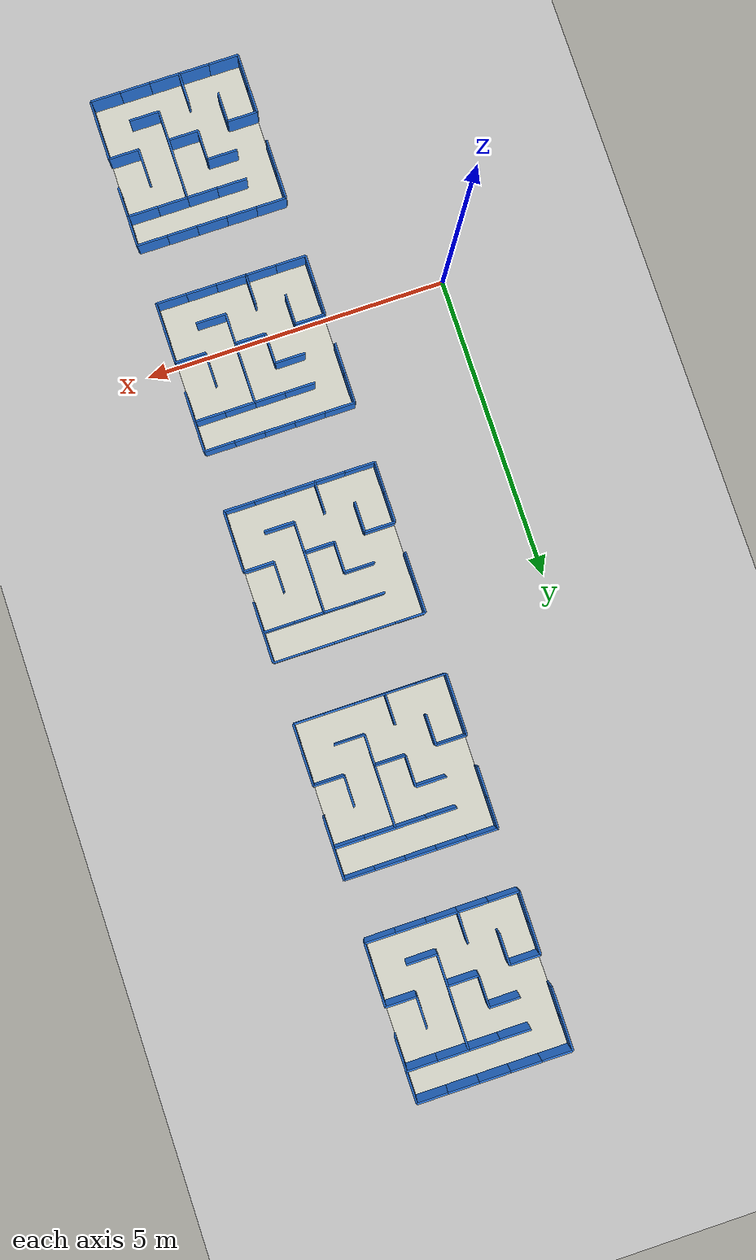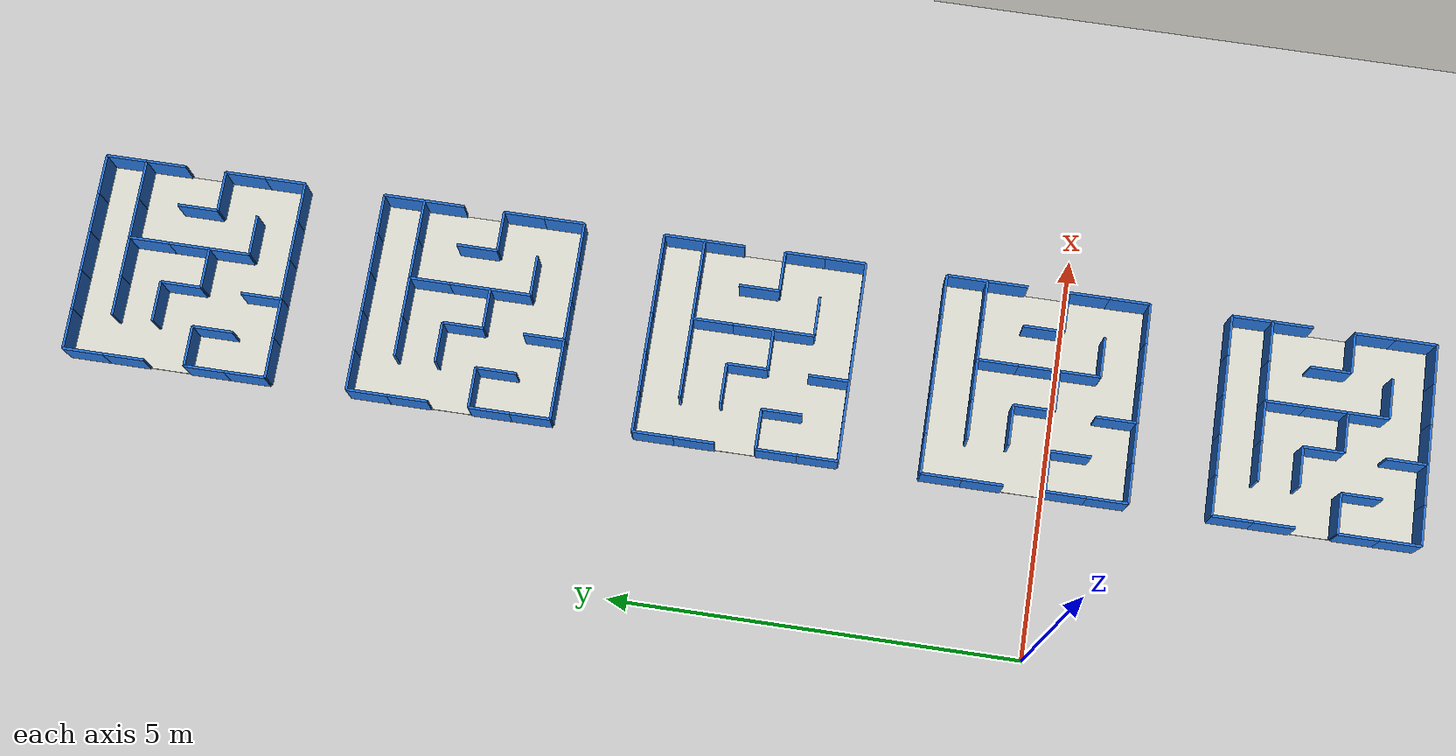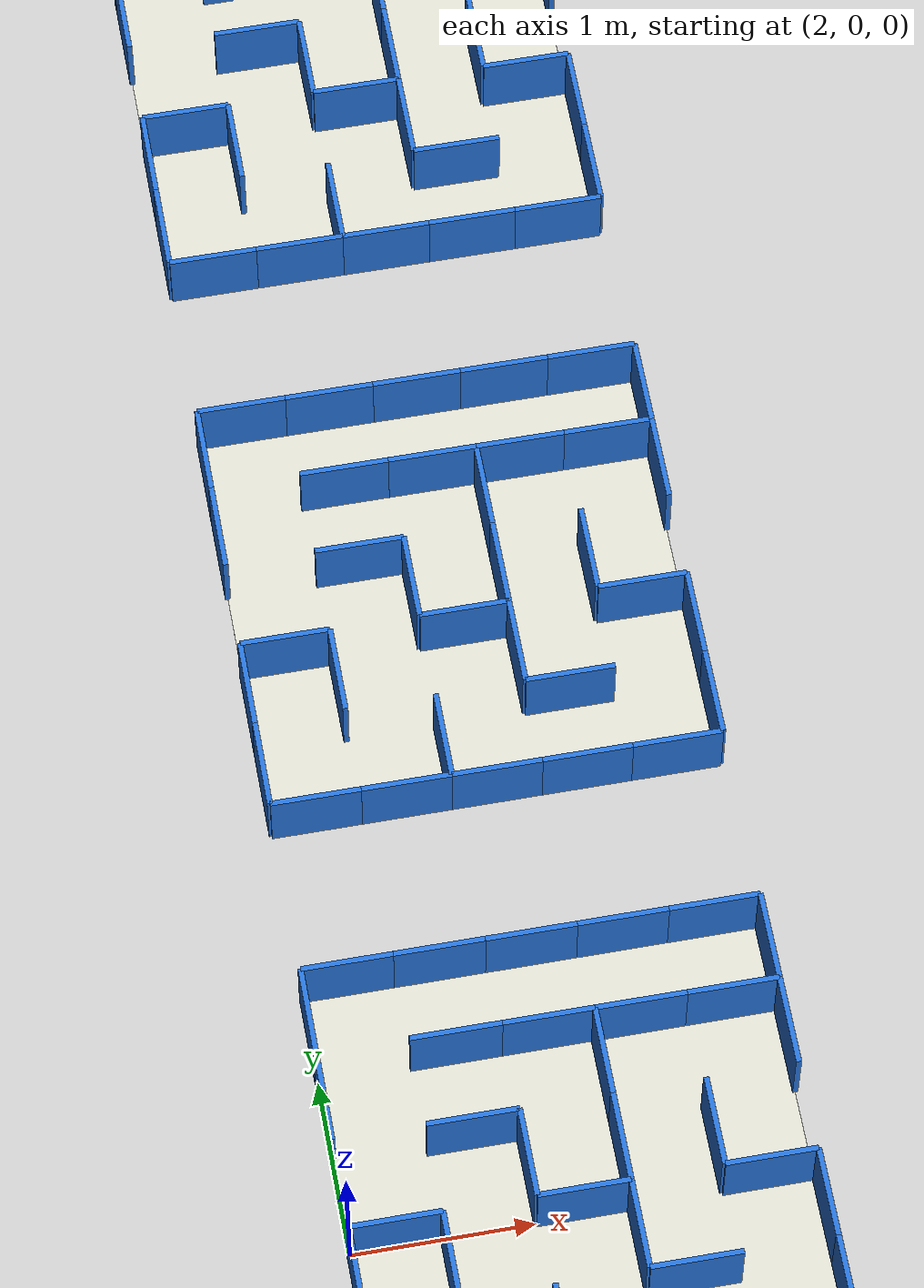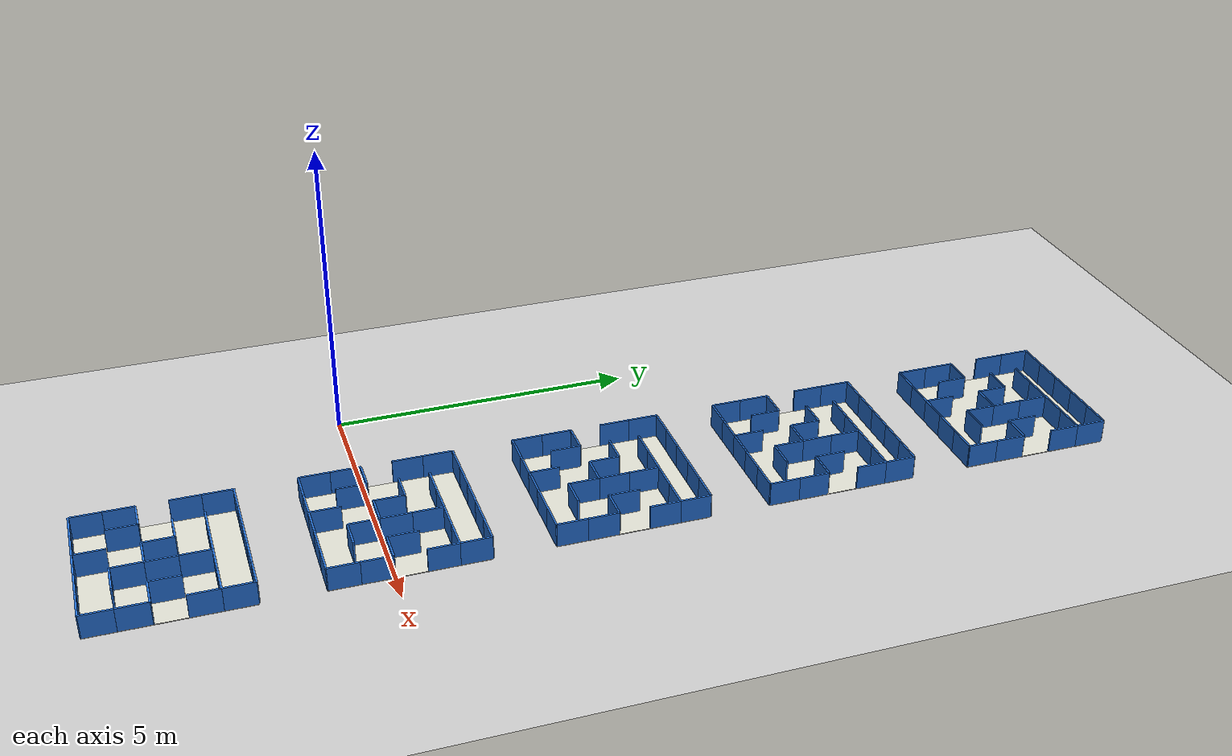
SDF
<?xml version="1.0" ?>
<sdf version="1.10">
  <world name="nhom8_mecanum">
    <physics name="1ms" type="ignored">
      <max_step_size>0.001</max_step_size>
      <real_time_factor>1.0</real_time_factor>
    </physics>
    <plugin filename="gz-sim-physics-system" name="gz::sim::systems::Physics" />
    <plugin filename="gz-sim-user-commands-system" name="gz::sim::systems::UserCommands" />
    <plugin filename="gz-sim-scene-broadcaster-system" name="gz::sim::systems::SceneBroadcaster" />
    <plugin filename="gz-sim-sensors-system" name="gz::sim::systems::Sensors">
      <render_engine>ogre2</render_engine>
    </plugin>
    <light type="directional" name="sun">
      <cast_shadows>true</cast_shadows>
      <pose>0 0 10 0 0 0</pose>
      <diffuse>1 1 1 1</diffuse>
      <specular>0.5 0.5 0.5 1</specular>
      <attenuation>
        <range>1000</range>
        <constant>0.9</constant>
        <linear>0.01</linear>
        <quadratic>0.001</quadratic>
      </attenuation>
      <direction>-0.5 0.1 -0.9</direction>
    </light>
    <model name="ground_plane">
      <static>true</static>
      <link name="link">
        <collision name="collision">
          <geometry>
            <plane>
              <normal>0 0 1</normal>
              <size>50 50</size>
            </plane>
          </geometry>
          <surface>
            <friction>
              <ode>
                <mu>40</mu>
              </ode>
            </friction>
          </surface>
        </collision>
        <visual name="visual">
          <geometry>
            <plane>
              <normal>0 0 1</normal>
              <size>50 50</size>
            </plane>
          </geometry>
          <material>
            <ambient>0.8 0.8 0.8 1</ambient>
            <diffuse>0.8 0.8 0.8 1</diffuse>
            <specular>0.8 0.8 0.8 1</specular>
          </material>
        </visual>
      </link>
    </model>
    <model name="hw_0_0">
      <static>true</static>
      <pose>2.0000 -4.2500 0.2000 0 0 1.5708</pose>
      <link name="link">
        <collision name="col">
          <geometry>
            <box>
              <size>0.5000 0.0300 0.4000</size>
            </box>
          </geometry>
        </collision>
        <visual name="vis">
          <geometry>
            <box>
              <size>0.5000 0.0300 0.4000</size>
            </box>
          </geometry>
          <material>
            <ambient>0.15 0.45 0.85 1</ambient>
            <diffuse>0.15 0.45 0.85 1</diffuse>
          </material>
        </visual>
      </link>
    </model>
    <model name="hw_0_1">
      <static>true</static>
      <pose>2.0000 -3.7500 0.2000 0 0 1.5708</pose>
      <link name="link">
        <collision name="col">
          <geometry>
            <box>
              <size>0.5000 0.0300 0.4000</size>
            </box>
          </geometry>
        </collision>
        <visual name="vis">
          <geometry>
            <box>
              <size>0.5000 0.0300 0.4000</size>
            </box>
          </geometry>
          <material>
            <ambient>0.15 0.45 0.85 1</ambient>
            <diffuse>0.15 0.45 0.85 1</diffuse>
          </material>
        </visual>
      </link>
    </model>
    <model name="hw_0_3">
      <static>true</static>
      <pose>2.0000 -2.7500 0.2000 0 0 1.5708</pose>
      <link name="link">
        <collision name="col">
          <geometry>
            <box>
              <size>0.5000 0.0300 0.4000</size>
            </box>
          </geometry>
        </collision>
        <visual name="vis">
          <geometry>
            <box>
              <size>0.5000 0.0300 0.4000</size>
            </box>
          </geometry>
          <material>
            <ambient>0.15 0.45 0.85 1</ambient>
            <diffuse>0.15 0.45 0.85 1</diffuse>
          </material>
        </visual>
      </link>
    </model>
    <model name="hw_0_4">
      <static>true</static>
      <pose>2.0000 -2.2500 0.2000 0 0 1.5708</pose>
      <link name="link">
        <collision name="col">
          <geometry>
            <box>
              <size>0.5000 0.0300 0.4000</size>
            </box>
          </geometry>
        </collision>
        <visual name="vis">
          <geometry>
            <box>
              <size>0.5000 0.0300 0.4000</size>
            </box>
          </geometry>
          <material>
            <ambient>0.15 0.45 0.85 1</ambient>
            <diffuse>0.15 0.45 0.85 1</diffuse>
          </material>
        </visual>
      </link>
    </model>
    <model name="hw_1_1">
      <static>true</static>
      <pose>2.5000 -3.7500 0.2000 0 0 1.5708</pose>
      <link name="link">
        <collision name="col">
          <geometry>
            <box>
              <size>0.5000 0.0300 0.4000</size>
            </box>
          </geometry>
        </collision>
        <visual name="vis">
          <geometry>
            <box>
              <size>0.5000 0.0300 0.4000</size>
            </box>
          </geometry>
          <material>
            <ambient>0.15 0.45 0.85 1</ambient>
            <diffuse>0.15 0.45 0.85 1</diffuse>
          </material>
        </visual>
      </link>
    </model>
    <model name="hw_2_0">
      <static>true</static>
      <pose>3.0000 -4.2500 0.2000 0 0 1.5708</pose>
      <link name="link">
        <collision name="col">
          <geometry>
            <box>
              <size>0.5000 0.0300 0.4000</size>
            </box>
          </geometry>
        </collision>
        <visual name="vis">
          <geometry>
            <box>
              <size>0.5000 0.0300 0.4000</size>
            </box>
          </geometry>
          <material>
            <ambient>0.15 0.45 0.85 1</ambient>
            <diffuse>0.15 0.45 0.85 1</diffuse>
          </material>
        </visual>
      </link>
    </model>
    <model name="hw_2_2">
      <static>true</static>
      <pose>3.0000 -3.2500 0.2000 0 0 1.5708</pose>
      <link name="link">
        <collision name="col">
          <geometry>
            <box>
              <size>0.5000 0.0300 0.4000</size>
            </box>
          </geometry>
        </collision>
        <visual name="vis">
          <geometry>
            <box>
              <size>0.5000 0.0300 0.4000</size>
            </box>
          </geometry>
          <material>
            <ambient>0.15 0.45 0.85 1</ambient>
            <diffuse>0.15 0.45 0.85 1</diffuse>
          </material>
        </visual>
      </link>
    </model>
    <model name="hw_3_1">
      <static>true</static>
      <pose>3.5000 -3.7500 0.2000 0 0 1.5708</pose>
      <link name="link">
        <collision name="col">
          <geometry>
            <box>
              <size>0.5000 0.0300 0.4000</size>
            </box>
          </geometry>
        </collision>
        <visual name="vis">
          <geometry>
            <box>
              <size>0.5000 0.0300 0.4000</size>
            </box>
          </geometry>
          <material>
            <ambient>0.15 0.45 0.85 1</ambient>
            <diffuse>0.15 0.45 0.85 1</diffuse>
          </material>
        </visual>
      </link>
    </model>
    <model name="hw_3_2">
      <static>true</static>
      <pose>3.5000 -3.2500 0.2000 0 0 1.5708</pose>
      <link name="link">
        <collision name="col">
          <geometry>
            <box>
              <size>0.5000 0.0300 0.4000</size>
            </box>
          </geometry>
        </collision>
        <visual name="vis">
          <geometry>
            <box>
              <size>0.5000 0.0300 0.4000</size>
            </box>
          </geometry>
          <material>
            <ambient>0.15 0.45 0.85 1</ambient>
            <diffuse>0.15 0.45 0.85 1</diffuse>
          </material>
        </visual>
      </link>
    </model>
    <model name="hw_3_3">
      <static>true</static>
      <pose>3.5000 -2.7500 0.2000 0 0 1.5708</pose>
      <link name="link">
        <collision name="col">
          <geometry>
            <box>
              <size>0.5000 0.0300 0.4000</size>
            </box>
          </geometry>
        </collision>
        <visual name="vis">
          <geometry>
            <box>
              <size>0.5000 0.0300 0.4000</size>
            </box>
          </geometry>
          <material>
            <ambient>0.15 0.45 0.85 1</ambient>
            <diffuse>0.15 0.45 0.85 1</diffuse>
          </material>
        </visual>
      </link>
    </model>
    <model name="hw_4_2">
      <static>true</static>
      <pose>4.0000 -3.2500 0.2000 0 0 1.5708</pose>
      <link name="link">
        <collision name="col">
          <geometry>
            <box>
              <size>0.5000 0.0300 0.4000</size>
            </box>
          </geometry>
        </collision>
        <visual name="vis">
          <geometry>
            <box>
              <size>0.5000 0.0300 0.4000</size>
            </box>
          </geometry>
          <material>
            <ambient>0.15 0.45 0.85 1</ambient>
            <diffuse>0.15 0.45 0.85 1</diffuse>
          </material>
        </visual>
      </link>
    </model>
    <model name="hw_5_0">
      <static>true</static>
      <pose>4.5000 -4.2500 0.2000 0 0 1.5708</pose>
      <link name="link">
        <collision name="col">
          <geometry>
            <box>
              <size>0.5000 0.0300 0.4000</size>
            </box>
          </geometry>
        </collision>
        <visual name="vis">
          <geometry>
            <box>
              <size>0.5000 0.0300 0.4000</size>
            </box>
          </geometry>
          <material>
            <ambient>0.15 0.45 0.85 1</ambient>
            <diffuse>0.15 0.45 0.85 1</diffuse>
          </material>
        </visual>
      </link>
    </model>
    <model name="hw_5_1">
      <static>true</static>
      <pose>4.5000 -3.7500 0.2000 0 0 1.5708</pose>
      <link name="link">
        <collision name="col">
          <geometry>
            <box>
              <size>0.5000 0.0300 0.4000</size>
            </box>
          </geometry>
        </collision>
        <visual name="vis">
          <geometry>
            <box>
              <size>0.5000 0.0300 0.4000</size>
            </box>
          </geometry>
          <material>
            <ambient>0.15 0.45 0.85 1</ambient>
            <diffuse>0.15 0.45 0.85 1</diffuse>
          </material>
        </visual>
      </link>
    </model>
    <model name="hw_5_3">
      <static>true</static>
      <pose>4.5000 -2.7500 0.2000 0 0 1.5708</pose>
      <link name="link">
        <collision name="col">
          <geometry>
            <box>
              <size>0.5000 0.0300 0.4000</size>
            </box>
          </geometry>
        </collision>
        <visual name="vis">
          <geometry>
            <box>
              <size>0.5000 0.0300 0.4000</size>
            </box>
          </geometry>
          <material>
            <ambient>0.15 0.45 0.85 1</ambient>
            <diffuse>0.15 0.45 0.85 1</diffuse>
          </material>
        </visual>
      </link>
    </model>
    <model name="hw_5_4">
      <static>true</static>
      <pose>4.5000 -2.2500 0.2000 0 0 1.5708</pose>
      <link name="link">
        <collision name="col">
          <geometry>
            <box>
              <size>0.5000 0.0300 0.4000</size>
            </box>
          </geometry>
        </collision>
        <visual name="vis">
          <geometry>
            <box>
              <size>0.5000 0.0300 0.4000</size>
            </box>
          </geometry>
          <material>
            <ambient>0.15 0.45 0.85 1</ambient>
            <diffuse>0.15 0.45 0.85 1</diffuse>
          </material>
        </visual>
      </link>
    </model>
    <model name="vw_0_0">
      <static>true</static>
      <pose>2.2500 -4.5000 0.2000 0 0 1.5708</pose>
      <link name="link">
        <collision name="col">
          <geometry>
            <box>
              <size>0.0300 0.5000 0.4000</size>
            </box>
          </geometry>
        </collision>
        <visual name="vis">
          <geometry>
            <box>
              <size>0.0300 0.5000 0.4000</size>
            </box>
          </geometry>
          <material>
            <ambient>0.15 0.45 0.85 1</ambient>
            <diffuse>0.15 0.45 0.85 1</diffuse>
          </material>
        </visual>
      </link>
    </model>
    <model name="vw_0_2">
      <static>true</static>
      <pose>2.2500 -3.5000 0.2000 0 0 1.5708</pose>
      <link name="link">
        <collision name="col">
          <geometry>
            <box>
              <size>0.0300 0.5000 0.4000</size>
            </box>
          </geometry>
        </collision>
        <visual name="vis">
          <geometry>
            <box>
              <size>0.0300 0.5000 0.4000</size>
            </box>
          </geometry>
          <material>
            <ambient>0.15 0.45 0.85 1</ambient>
            <diffuse>0.15 0.45 0.85 1</diffuse>
          </material>
        </visual>
      </link>
    </model>
    <model name="vw_0_5">
      <static>true</static>
      <pose>2.2500 -2.0000 0.2000 0 0 1.5708</pose>
      <link name="link">
        <collision name="col">
          <geometry>
            <box>
              <size>0.0300 0.5000 0.4000</size>
            </box>
          </geometry>
        </collision>
        <visual name="vis">
          <geometry>
            <box>
              <size>0.0300 0.5000 0.4000</size>
            </box>
          </geometry>
          <material>
            <ambient>0.15 0.45 0.85 1</ambient>
            <diffuse>0.15 0.45 0.85 1</diffuse>
          </material>
        </visual>
      </link>
    </model>
    <model name="vw_1_0">
      <static>true</static>
      <pose>2.7500 -4.5000 0.2000 0 0 1.5708</pose>
      <link name="link">
        <collision name="col">
          <geometry>
            <box>
              <size>0.0300 0.5000 0.4000</size>
            </box>
          </geometry>
        </collision>
        <visual name="vis">
          <geometry>
            <box>
              <size>0.0300 0.5000 0.4000</size>
            </box>
          </geometry>
          <material>
            <ambient>0.15 0.45 0.85 1</ambient>
            <diffuse>0.15 0.45 0.85 1</diffuse>
          </material>
        </visual>
      </link>
    </model>
    <model name="vw_1_3">
      <static>true</static>
      <pose>2.7500 -3.0000 0.2000 0 0 1.5708</pose>
      <link name="link">
        <collision name="col">
          <geometry>
            <box>
              <size>0.0300 0.5000 0.4000</size>
            </box>
          </geometry>
        </collision>
        <visual name="vis">
          <geometry>
            <box>
              <size>0.0300 0.5000 0.4000</size>
            </box>
          </geometry>
          <material>
            <ambient>0.15 0.45 0.85 1</ambient>
            <diffuse>0.15 0.45 0.85 1</diffuse>
          </material>
        </visual>
      </link>
    </model>
    <model name="vw_1_4">
      <static>true</static>
      <pose>2.7500 -2.5000 0.2000 0 0 1.5708</pose>
      <link name="link">
        <collision name="col">
          <geometry>
            <box>
              <size>0.0300 0.5000 0.4000</size>
            </box>
          </geometry>
        </collision>
        <visual name="vis">
          <geometry>
            <box>
              <size>0.0300 0.5000 0.4000</size>
            </box>
          </geometry>
          <material>
            <ambient>0.15 0.45 0.85 1</ambient>
            <diffuse>0.15 0.45 0.85 1</diffuse>
          </material>
        </visual>
      </link>
    </model>
    <model name="vw_1_5">
      <static>true</static>
      <pose>2.7500 -2.0000 0.2000 0 0 1.5708</pose>
      <link name="link">
        <collision name="col">
          <geometry>
            <box>
              <size>0.0300 0.5000 0.4000</size>
            </box>
          </geometry>
        </collision>
        <visual name="vis">
          <geometry>
            <box>
              <size>0.0300 0.5000 0.4000</size>
            </box>
          </geometry>
          <material>
            <ambient>0.15 0.45 0.85 1</ambient>
            <diffuse>0.15 0.45 0.85 1</diffuse>
          </material>
        </visual>
      </link>
    </model>
    <model name="vw_2_0">
      <static>true</static>
      <pose>3.2500 -4.5000 0.2000 0 0 1.5708</pose>
      <link name="link">
        <collision name="col">
          <geometry>
            <box>
              <size>0.0300 0.5000 0.4000</size>
            </box>
          </geometry>
        </collision>
        <visual name="vis">
          <geometry>
            <box>
              <size>0.0300 0.5000 0.4000</size>
            </box>
          </geometry>
          <material>
            <ambient>0.15 0.45 0.85 1</ambient>
            <diffuse>0.15 0.45 0.85 1</diffuse>
          </material>
        </visual>
      </link>
    </model>
    <model name="vw_2_2">
      <static>true</static>
      <pose>3.2500 -3.5000 0.2000 0 0 1.5708</pose>
      <link name="link">
        <collision name="col">
          <geometry>
            <box>
              <size>0.0300 0.5000 0.4000</size>
            </box>
          </geometry>
        </collision>
        <visual name="vis">
          <geometry>
            <box>
              <size>0.0300 0.5000 0.4000</size>
            </box>
          </geometry>
          <material>
            <ambient>0.15 0.45 0.85 1</ambient>
            <diffuse>0.15 0.45 0.85 1</diffuse>
          </material>
        </visual>
      </link>
    </model>
    <model name="vw_2_4">
      <static>true</static>
      <pose>3.2500 -2.5000 0.2000 0 0 1.5708</pose>
      <link name="link">
        <collision name="col">
          <geometry>
            <box>
              <size>0.0300 0.5000 0.4000</size>
            </box>
          </geometry>
        </collision>
        <visual name="vis">
          <geometry>
            <box>
              <size>0.0300 0.5000 0.4000</size>
            </box>
          </geometry>
          <material>
            <ambient>0.15 0.45 0.85 1</ambient>
            <diffuse>0.15 0.45 0.85 1</diffuse>
          </material>
        </visual>
      </link>
    </model>
    <model name="vw_2_5">
      <static>true</static>
      <pose>3.2500 -2.0000 0.2000 0 0 1.5708</pose>
      <link name="link">
        <collision name="col">
          <geometry>
            <box>
              <size>0.0300 0.5000 0.4000</size>
            </box>
          </geometry>
        </collision>
        <visual name="vis">
          <geometry>
            <box>
              <size>0.0300 0.5000 0.4000</size>
            </box>
          </geometry>
          <material>
            <ambient>0.15 0.45 0.85 1</ambient>
            <diffuse>0.15 0.45 0.85 1</diffuse>
          </material>
        </visual>
      </link>
    </model>
    <model name="vw_3_0">
      <static>true</static>
      <pose>3.7500 -4.5000 0.2000 0 0 1.5708</pose>
      <link name="link">
        <collision name="col">
          <geometry>
            <box>
              <size>0.0300 0.5000 0.4000</size>
            </box>
          </geometry>
        </collision>
        <visual name="vis">
          <geometry>
            <box>
              <size>0.0300 0.5000 0.4000</size>
            </box>
          </geometry>
          <material>
            <ambient>0.15 0.45 0.85 1</ambient>
            <diffuse>0.15 0.45 0.85 1</diffuse>
          </material>
        </visual>
      </link>
    </model>
    <model name="vw_3_1">
      <static>true</static>
      <pose>3.7500 -4.0000 0.2000 0 0 1.5708</pose>
      <link name="link">
        <collision name="col">
          <geometry>
            <box>
              <size>0.0300 0.5000 0.4000</size>
            </box>
          </geometry>
        </collision>
        <visual name="vis">
          <geometry>
            <box>
              <size>0.0300 0.5000 0.4000</size>
            </box>
          </geometry>
          <material>
            <ambient>0.15 0.45 0.85 1</ambient>
            <diffuse>0.15 0.45 0.85 1</diffuse>
          </material>
        </visual>
      </link>
    </model>
    <model name="vw_3_4">
      <static>true</static>
      <pose>3.7500 -2.5000 0.2000 0 0 1.5708</pose>
      <link name="link">
        <collision name="col">
          <geometry>
            <box>
              <size>0.0300 0.5000 0.4000</size>
            </box>
          </geometry>
        </collision>
        <visual name="vis">
          <geometry>
            <box>
              <size>0.0300 0.5000 0.4000</size>
            </box>
          </geometry>
          <material>
            <ambient>0.15 0.45 0.85 1</ambient>
            <diffuse>0.15 0.45 0.85 1</diffuse>
          </material>
        </visual>
      </link>
    </model>
    <model name="vw_3_5">
      <static>true</static>
      <pose>3.7500 -2.0000 0.2000 0 0 1.5708</pose>
      <link name="link">
        <collision name="col">
          <geometry>
            <box>
              <size>0.0300 0.5000 0.4000</size>
            </box>
          </geometry>
        </collision>
        <visual name="vis">
          <geometry>
            <box>
              <size>0.0300 0.5000 0.4000</size>
            </box>
          </geometry>
          <material>
            <ambient>0.15 0.45 0.85 1</ambient>
            <diffuse>0.15 0.45 0.85 1</diffuse>
          </material>
        </visual>
      </link>
    </model>
    <model name="vw_4_0">
      <static>true</static>
      <pose>4.2500 -4.5000 0.2000 0 0 1.5708</pose>
      <link name="link">
        <collision name="col">
          <geometry>
            <box>
              <size>0.0300 0.5000 0.4000</size>
            </box>
          </geometry>
        </collision>
        <visual name="vis">
          <geometry>
            <box>
              <size>0.0300 0.5000 0.4000</size>
            </box>
          </geometry>
          <material>
            <ambient>0.15 0.45 0.85 1</ambient>
            <diffuse>0.15 0.45 0.85 1</diffuse>
          </material>
        </visual>
      </link>
    </model>
    <model name="vw_4_2">
      <static>true</static>
      <pose>4.2500 -3.5000 0.2000 0 0 1.5708</pose>
      <link name="link">
        <collision name="col">
          <geometry>
            <box>
              <size>0.0300 0.5000 0.4000</size>
            </box>
          </geometry>
        </collision>
        <visual name="vis">
          <geometry>
            <box>
              <size>0.0300 0.5000 0.4000</size>
            </box>
          </geometry>
          <material>
            <ambient>0.15 0.45 0.85 1</ambient>
            <diffuse>0.15 0.45 0.85 1</diffuse>
          </material>
        </visual>
      </link>
    </model>
    <model name="vw_4_4">
      <static>true</static>
      <pose>4.2500 -2.5000 0.2000 0 0 1.5708</pose>
      <link name="link">
        <collision name="col">
          <geometry>
            <box>
              <size>0.0300 0.5000 0.4000</size>
            </box>
          </geometry>
        </collision>
        <visual name="vis">
          <geometry>
            <box>
              <size>0.0300 0.5000 0.4000</size>
            </box>
          </geometry>
          <material>
            <ambient>0.15 0.45 0.85 1</ambient>
            <diffuse>0.15 0.45 0.85 1</diffuse>
          </material>
        </visual>
      </link>
    </model>
    <model name="vw_4_5">
      <static>true</static>
      <pose>4.2500 -2.0000 0.2000 0 0 1.5708</pose>
      <link name="link">
        <collision name="col">
          <geometry>
            <box>
              <size>0.0300 0.5000 0.4000</size>
            </box>
          </geometry>
        </collision>
        <visual name="vis">
          <geometry>
            <box>
              <size>0.0300 0.5000 0.4000</size>
            </box>
          </geometry>
          <material>
            <ambient>0.15 0.45 0.85 1</ambient>
            <diffuse>0.15 0.45 0.85 1</diffuse>
          </material>
        </visual>
      </link>
    </model>
    <model name="floor">
      <static>true</static>
      <pose>3.2500 -3.2500 -0.02 0 0 1.5708</pose>
      <link name="link">
        <collision name="col">
          <geometry>
            <box>
              <size>2.50 2.50 0.03</size>
            </box>
          </geometry>
        </collision>
        <visual name="vis">
          <geometry>
            <box>
              <size>2.50 2.50 0.03</size>
            </box>
          </geometry>
          <material>
            <ambient>0.87 0.87 0.82 1</ambient>
            <diffuse>0.87 0.87 0.82 1</diffuse>
          </material>
        </visual>
      </link>
    </model>
    <model name="hw_0_0_m1">
      <static>true</static>
      <pose>2.0000 -0.750000 0.2000 0 0 1.5708</pose>
      <link name="link">
        <collision name="col">
          <geometry>
            <box>
              <size>0.5000 0.0300 0.4000</size>
            </box>
          </geometry>
        </collision>
        <visual name="vis">
          <geometry>
            <box>
              <size>0.5000 0.0300 0.4000</size>
            </box>
          </geometry>
          <material>
            <ambient>0.15 0.45 0.85 1</ambient>
            <diffuse>0.15 0.45 0.85 1</diffuse>
          </material>
        </visual>
      </link>
    </model>
    <model name="hw_0_1_m1">
      <static>true</static>
      <pose>2.0000 -0.250000 0.2000 0 0 1.5708</pose>
      <link name="link">
        <collision name="col">
          <geometry>
            <box>
              <size>0.5000 0.0300 0.4000</size>
            </box>
          </geometry>
        </collision>
        <visual name="vis">
          <geometry>
            <box>
              <size>0.5000 0.0300 0.4000</size>
            </box>
          </geometry>
          <material>
            <ambient>0.15 0.45 0.85 1</ambient>
            <diffuse>0.15 0.45 0.85 1</diffuse>
          </material>
        </visual>
      </link>
    </model>
    <model name="hw_0_3_m1">
      <static>true</static>
      <pose>2.0000 0.750000 0.2000 0 0 1.5708</pose>
      <link name="link">
        <collision name="col">
          <geometry>
            <box>
              <size>0.5000 0.0300 0.4000</size>
            </box>
          </geometry>
        </collision>
        <visual name="vis">
          <geometry>
            <box>
              <size>0.5000 0.0300 0.4000</size>
            </box>
          </geometry>
          <material>
            <ambient>0.15 0.45 0.85 1</ambient>
            <diffuse>0.15 0.45 0.85 1</diffuse>
          </material>
        </visual>
      </link>
    </model>
    <model name="hw_0_4_m1">
      <static>true</static>
      <pose>2.0000 1.250000 0.2000 0 0 1.5708</pose>
      <link name="link">
        <collision name="col">
          <geometry>
            <box>
              <size>0.5000 0.0300 0.4000</size>
            </box>
          </geometry>
        </collision>
        <visual name="vis">
          <geometry>
            <box>
              <size>0.5000 0.0300 0.4000</size>
            </box>
          </geometry>
          <material>
            <ambient>0.15 0.45 0.85 1</ambient>
            <diffuse>0.15 0.45 0.85 1</diffuse>
          </material>
        </visual>
      </link>
    </model>
    <model name="hw_1_1_m1">
      <static>true</static>
      <pose>2.5000 -0.250000 0.2000 0 0 1.5708</pose>
      <link name="link">
        <collision name="col">
          <geometry>
            <box>
              <size>0.5000 0.0300 0.4000</size>
            </box>
          </geometry>
        </collision>
        <visual name="vis">
          <geometry>
            <box>
              <size>0.5000 0.0300 0.4000</size>
            </box>
          </geometry>
          <material>
            <ambient>0.15 0.45 0.85 1</ambient>
            <diffuse>0.15 0.45 0.85 1</diffuse>
          </material>
        </visual>
      </link>
    </model>
    <model name="hw_2_0_m1">
      <static>true</static>
      <pose>3.0000 -0.750000 0.2000 0 0 1.5708</pose>
      <link name="link">
        <collision name="col">
          <geometry>
            <box>
              <size>0.5000 0.0300 0.4000</size>
            </box>
          </geometry>
        </collision>
        <visual name="vis">
          <geometry>
            <box>
              <size>0.5000 0.0300 0.4000</size>
            </box>
          </geometry>
          <material>
            <ambient>0.15 0.45 0.85 1</ambient>
            <diffuse>0.15 0.45 0.85 1</diffuse>
          </material>
        </visual>
      </link>
    </model>
    <model name="hw_2_2_m1">
      <static>true</static>
      <pose>3.0000 0.250000 0.2000 0 0 1.5708</pose>
      <link name="link">
        <collision name="col">
          <geometry>
            <box>
              <size>0.5000 0.0300 0.4000</size>
            </box>
          </geometry>
        </collision>
        <visual name="vis">
          <geometry>
            <box>
              <size>0.5000 0.0300 0.4000</size>
            </box>
          </geometry>
          <material>
            <ambient>0.15 0.45 0.85 1</ambient>
            <diffuse>0.15 0.45 0.85 1</diffuse>
          </material>
        </visual>
      </link>
    </model>
    <model name="hw_3_1_m1">
      <static>true</static>
      <pose>3.5000 -0.250000 0.2000 0 0 1.5708</pose>
      <link name="link">
        <collision name="col">
          <geometry>
            <box>
              <size>0.5000 0.0300 0.4000</size>
            </box>
          </geometry>
        </collision>
        <visual name="vis">
          <geometry>
            <box>
              <size>0.5000 0.0300 0.4000</size>
            </box>
          </geometry>
          <material>
            <ambient>0.15 0.45 0.85 1</ambient>
            <diffuse>0.15 0.45 0.85 1</diffuse>
          </material>
        </visual>
      </link>
    </model>
    <model name="hw_3_2_m1">
      <static>true</static>
      <pose>3.5000 0.250000 0.2000 0 0 1.5708</pose>
      <link name="link">
        <collision name="col">
          <geometry>
            <box>
              <size>0.5000 0.0300 0.4000</size>
            </box>
          </geometry>
        </collision>
        <visual name="vis">
          <geometry>
            <box>
              <size>0.5000 0.0300 0.4000</size>
            </box>
          </geometry>
          <material>
            <ambient>0.15 0.45 0.85 1</ambient>
            <diffuse>0.15 0.45 0.85 1</diffuse>
          </material>
        </visual>
      </link>
    </model>
    <model name="hw_3_3_m1">
      <static>true</static>
      <pose>3.5000 0.750000 0.2000 0 0 1.5708</pose>
      <link name="link">
        <collision name="col">
          <geometry>
            <box>
              <size>0.5000 0.0300 0.4000</size>
            </box>
          </geometry>
        </collision>
        <visual name="vis">
          <geometry>
            <box>
              <size>0.5000 0.0300 0.4000</size>
            </box>
          </geometry>
          <material>
            <ambient>0.15 0.45 0.85 1</ambient>
            <diffuse>0.15 0.45 0.85 1</diffuse>
          </material>
        </visual>
      </link>
    </model>
    <model name="hw_4_2_m1">
      <static>true</static>
      <pose>4.0000 0.250000 0.2000 0 0 1.5708</pose>
      <link name="link">
        <collision name="col">
          <geometry>
            <box>
              <size>0.5000 0.0300 0.4000</size>
            </box>
          </geometry>
        </collision>
        <visual name="vis">
          <geometry>
            <box>
              <size>0.5000 0.0300 0.4000</size>
            </box>
          </geometry>
          <material>
            <ambient>0.15 0.45 0.85 1</ambient>
            <diffuse>0.15 0.45 0.85 1</diffuse>
          </material>
        </visual>
      </link>
    </model>
    <model name="hw_5_0_m1">
      <static>true</static>
      <pose>4.5000 -0.750000 0.2000 0 0 1.5708</pose>
      <link name="link">
        <collision name="col">
          <geometry>
            <box>
              <size>0.5000 0.0300 0.4000</size>
            </box>
          </geometry>
        </collision>
        <visual name="vis">
          <geometry>
            <box>
              <size>0.5000 0.0300 0.4000</size>
            </box>
          </geometry>
          <material>
            <ambient>0.15 0.45 0.85 1</ambient>
            <diffuse>0.15 0.45 0.85 1</diffuse>
          </material>
        </visual>
      </link>
    </model>
    <model name="hw_5_1_m1">
      <static>true</static>
      <pose>4.5000 -0.250000 0.2000 0 0 1.5708</pose>
      <link name="link">
        <collision name="col">
          <geometry>
            <box>
              <size>0.5000 0.0300 0.4000</size>
            </box>
          </geometry>
        </collision>
        <visual name="vis">
          <geometry>
            <box>
              <size>0.5000 0.0300 0.4000</size>
            </box>
          </geometry>
          <material>
            <ambient>0.15 0.45 0.85 1</ambient>
            <diffuse>0.15 0.45 0.85 1</diffuse>
          </material>
        </visual>
      </link>
    </model>
    <model name="hw_5_3_m1">
      <static>true</static>
      <pose>4.5000 0.750000 0.2000 0 0 1.5708</pose>
      <link name="link">
        <collision name="col">
          <geometry>
            <box>
              <size>0.5000 0.0300 0.4000</size>
            </box>
          </geometry>
        </collision>
        <visual name="vis">
          <geometry>
            <box>
              <size>0.5000 0.0300 0.4000</size>
            </box>
          </geometry>
          <material>
            <ambient>0.15 0.45 0.85 1</ambient>
            <diffuse>0.15 0.45 0.85 1</diffuse>
          </material>
        </visual>
      </link>
    </model>
    <model name="hw_5_4_m1">
      <static>true</static>
      <pose>4.5000 1.250000 0.2000 0 0 1.5708</pose>
      <link name="link">
        <collision name="col">
          <geometry>
            <box>
              <size>0.5000 0.0300 0.4000</size>
            </box>
          </geometry>
        </collision>
        <visual name="vis">
          <geometry>
            <box>
              <size>0.5000 0.0300 0.4000</size>
            </box>
          </geometry>
          <material>
            <ambient>0.15 0.45 0.85 1</ambient>
            <diffuse>0.15 0.45 0.85 1</diffuse>
          </material>
        </visual>
      </link>
    </model>
    <model name="vw_0_0_m1">
      <static>true</static>
      <pose>2.2500 -1.000000 0.2000 0 0 1.5708</pose>
      <link name="link">
        <collision name="col">
          <geometry>
            <box>
              <size>0.0300 0.5000 0.4000</size>
            </box>
          </geometry>
        </collision>
        <visual name="vis">
          <geometry>
            <box>
              <size>0.0300 0.5000 0.4000</size>
            </box>
          </geometry>
          <material>
            <ambient>0.15 0.45 0.85 1</ambient>
            <diffuse>0.15 0.45 0.85 1</diffuse>
          </material>
        </visual>
      </link>
    </model>
    <model name="vw_0_2_m1">
      <static>true</static>
      <pose>2.2500 0.000000 0.2000 0 0 1.5708</pose>
      <link name="link">
        <collision name="col">
          <geometry>
            <box>
              <size>0.0300 0.5000 0.4000</size>
            </box>
          </geometry>
        </collision>
        <visual name="vis">
          <geometry>
            <box>
              <size>0.0300 0.5000 0.4000</size>
            </box>
          </geometry>
          <material>
            <ambient>0.15 0.45 0.85 1</ambient>
            <diffuse>0.15 0.45 0.85 1</diffuse>
          </material>
        </visual>
      </link>
    </model>
    <model name="vw_0_5_m1">
      <static>true</static>
      <pose>2.2500 1.500000 0.2000 0 0 1.5708</pose>
      <link name="link">
        <collision name="col">
          <geometry>
            <box>
              <size>0.0300 0.5000 0.4000</size>
            </box>
          </geometry>
        </collision>
        <visual name="vis">
          <geometry>
            <box>
              <size>0.0300 0.5000 0.4000</size>
            </box>
          </geometry>
          <material>
            <ambient>0.15 0.45 0.85 1</ambient>
            <diffuse>0.15 0.45 0.85 1</diffuse>
          </material>
        </visual>
      </link>
    </model>
    <model name="vw_1_0_m1">
      <static>true</static>
      <pose>2.7500 -1.000000 0.2000 0 0 1.5708</pose>
      <link name="link">
        <collision name="col">
          <geometry>
            <box>
              <size>0.0300 0.5000 0.4000</size>
            </box>
          </geometry>
        </collision>
        <visual name="vis">
          <geometry>
            <box>
              <size>0.0300 0.5000 0.4000</size>
            </box>
          </geometry>
          <material>
            <ambient>0.15 0.45 0.85 1</ambient>
            <diffuse>0.15 0.45 0.85 1</diffuse>
          </material>
        </visual>
      </link>
    </model>
    <model name="vw_1_3_m1">
      <static>true</static>
      <pose>2.7500 0.500000 0.2000 0 0 1.5708</pose>
      <link name="link">
        <collision name="col">
          <geometry>
            <box>
              <size>0.0300 0.5000 0.4000</size>
            </box>
          </geometry>
        </collision>
        <visual name="vis">
          <geometry>
            <box>
              <size>0.0300 0.5000 0.4000</size>
            </box>
          </geometry>
          <material>
            <ambient>0.15 0.45 0.85 1</ambient>
            <diffuse>0.15 0.45 0.85 1</diffuse>
          </material>
        </visual>
      </link>
    </model>
    <model name="vw_1_4_m1">
      <static>true</static>
      <pose>2.7500 1.000000 0.2000 0 0 1.5708</pose>
      <link name="link">
        <collision name="col">
          <geometry>
            <box>
              <size>0.0300 0.5000 0.4000</size>
            </box>
          </geometry>
        </collision>
        <visual name="vis">
          <geometry>
            <box>
              <size>0.0300 0.5000 0.4000</size>
            </box>
          </geometry>
          <material>
            <ambient>0.15 0.45 0.85 1</ambient>
            <diffuse>0.15 0.45 0.85 1</diffuse>
          </material>
        </visual>
      </link>
    </model>
    <model name="vw_1_5_m1">
      <static>true</static>
      <pose>2.7500 1.500000 0.2000 0 0 1.5708</pose>
      <link name="link">
        <collision name="col">
          <geometry>
            <box>
              <size>0.0300 0.5000 0.4000</size>
            </box>
          </geometry>
        </collision>
        <visual name="vis">
          <geometry>
            <box>
              <size>0.0300 0.5000 0.4000</size>
            </box>
          </geometry>
          <material>
            <ambient>0.15 0.45 0.85 1</ambient>
            <diffuse>0.15 0.45 0.85 1</diffuse>
          </material>
        </visual>
      </link>
    </model>
    <model name="vw_2_0_m1">
      <static>true</static>
      <pose>3.2500 -1.000000 0.2000 0 0 1.5708</pose>
      <link name="link">
        <collision name="col">
          <geometry>
            <box>
              <size>0.0300 0.5000 0.4000</size>
            </box>
          </geometry>
        </collision>
        <visual name="vis">
          <geometry>
            <box>
              <size>0.0300 0.5000 0.4000</size>
            </box>
          </geometry>
          <material>
            <ambient>0.15 0.45 0.85 1</ambient>
            <diffuse>0.15 0.45 0.85 1</diffuse>
          </material>
        </visual>
      </link>
    </model>
    <model name="vw_2_2_m1">
      <static>true</static>
      <pose>3.2500 0.000000 0.2000 0 0 1.5708</pose>
      <link name="link">
        <collision name="col">
          <geometry>
            <box>
              <size>0.0300 0.5000 0.4000</size>
            </box>
          </geometry>
        </collision>
        <visual name="vis">
          <geometry>
            <box>
              <size>0.0300 0.5000 0.4000</size>
            </box>
          </geometry>
          <material>
            <ambient>0.15 0.45 0.85 1</ambient>
            <diffuse>0.15 0.45 0.85 1</diffuse>
          </material>
        </visual>
      </link>
    </model>
    <model name="vw_2_4_m1">
      <static>true</static>
      <pose>3.2500 1.000000 0.2000 0 0 1.5708</pose>
      <link name="link">
        <collision name="col">
          <geometry>
            <box>
              <size>0.0300 0.5000 0.4000</size>
            </box>
          </geometry>
        </collision>
        <visual name="vis">
          <geometry>
            <box>
              <size>0.0300 0.5000 0.4000</size>
            </box>
          </geometry>
          <material>
            <ambient>0.15 0.45 0.85 1</ambient>
            <diffuse>0.15 0.45 0.85 1</diffuse>
          </material>
        </visual>
      </link>
    </model>
    <model name="vw_2_5_m1">
      <static>true</static>
      <pose>3.2500 1.500000 0.2000 0 0 1.5708</pose>
      <link name="link">
        <collision name="col">
          <geometry>
            <box>
              <size>0.0300 0.5000 0.4000</size>
            </box>
          </geometry>
        </collision>
        <visual name="vis">
          <geometry>
            <box>
              <size>0.0300 0.5000 0.4000</size>
            </box>
          </geometry>
          <material>
            <ambient>0.15 0.45 0.85 1</ambient>
            <diffuse>0.15 0.45 0.85 1</diffuse>
          </material>
        </visual>
      </link>
    </model>
    <model name="vw_3_0_m1">
      <static>true</static>
      <pose>3.7500 -1.000000 0.2000 0 0 1.5708</pose>
      <link name="link">
        <collision name="col">
          <geometry>
            <box>
              <size>0.0300 0.5000 0.4000</size>
            </box>
          </geometry>
        </collision>
        <visual name="vis">
          <geometry>
            <box>
              <size>0.0300 0.5000 0.4000</size>
            </box>
          </geometry>
          <material>
            <ambient>0.15 0.45 0.85 1</ambient>
            <diffuse>0.15 0.45 0.85 1</diffuse>
          </material>
        </visual>
      </link>
    </model>
    <model name="vw_3_1_m1">
      <static>true</static>
      <pose>3.7500 -0.500000 0.2000 0 0 1.5708</pose>
      <link name="link">
        <collision name="col">
          <geometry>
            <box>
              <size>0.0300 0.5000 0.4000</size>
            </box>
          </geometry>
        </collision>
        <visual name="vis">
          <geometry>
            <box>
              <size>0.0300 0.5000 0.4000</size>
            </box>
          </geometry>
          <material>
            <ambient>0.15 0.45 0.85 1</ambient>
            <diffuse>0.15 0.45 0.85 1</diffuse>
          </material>
        </visual>
      </link>
    </model>
    <model name="vw_3_4_m1">
      <static>true</static>
      <pose>3.7500 1.000000 0.2000 0 0 1.5708</pose>
      <link name="link">
        <collision name="col">
          <geometry>
            <box>
              <size>0.0300 0.5000 0.4000</size>
            </box>
          </geometry>
        </collision>
        <visual name="vis">
          <geometry>
            <box>
              <size>0.0300 0.5000 0.4000</size>
            </box>
          </geometry>
          <material>
            <ambient>0.15 0.45 0.85 1</ambient>
            <diffuse>0.15 0.45 0.85 1</diffuse>
          </material>
        </visual>
      </link>
    </model>
    <model name="vw_3_5_m1">
      <static>true</static>
      <pose>3.7500 1.500000 0.2000 0 0 1.5708</pose>
      <link name="link">
        <collision name="col">
          <geometry>
            <box>
              <size>0.0300 0.5000 0.4000</size>
            </box>
          </geometry>
        </collision>
        <visual name="vis">
          <geometry>
            <box>
              <size>0.0300 0.5000 0.4000</size>
            </box>
          </geometry>
          <material>
            <ambient>0.15 0.45 0.85 1</ambient>
            <diffuse>0.15 0.45 0.85 1</diffuse>
          </material>
        </visual>
      </link>
    </model>
    <model name="vw_4_0_m1">
      <static>true</static>
      <pose>4.2500 -1.000000 0.2000 0 0 1.5708</pose>
      <link name="link">
        <collision name="col">
          <geometry>
            <box>
              <size>0.0300 0.5000 0.4000</size>
            </box>
          </geometry>
        </collision>
        <visual name="vis">
          <geometry>
            <box>
              <size>0.0300 0.5000 0.4000</size>
            </box>
          </geometry>
          <material>
            <ambient>0.15 0.45 0.85 1</ambient>
            <diffuse>0.15 0.45 0.85 1</diffuse>
          </material>
        </visual>
      </link>
    </model>
    <model name="vw_4_2_m1">
      <static>true</static>
      <pose>4.2500 0.000000 0.2000 0 0 1.5708</pose>
      <link name="link">
        <collision name="col">
          <geometry>
            <box>
              <size>0.0300 0.5000 0.4000</size>
            </box>
          </geometry>
        </collision>
        <visual name="vis">
          <geometry>
            <box>
              <size>0.0300 0.5000 0.4000</size>
            </box>
          </geometry>
          <material>
            <ambient>0.15 0.45 0.85 1</ambient>
            <diffuse>0.15 0.45 0.85 1</diffuse>
          </material>
        </visual>
      </link>
    </model>
    <model name="vw_4_4_m1">
      <static>true</static>
      <pose>4.2500 1.000000 0.2000 0 0 1.5708</pose>
      <link name="link">
        <collision name="col">
          <geometry>
            <box>
              <size>0.0300 0.5000 0.4000</size>
            </box>
          </geometry>
        </collision>
        <visual name="vis">
          <geometry>
            <box>
              <size>0.0300 0.5000 0.4000</size>
            </box>
          </geometry>
          <material>
            <ambient>0.15 0.45 0.85 1</ambient>
            <diffuse>0.15 0.45 0.85 1</diffuse>
          </material>
        </visual>
      </link>
    </model>
    <model name="vw_4_5_m1">
      <static>true</static>
      <pose>4.2500 1.500000 0.2000 0 0 1.5708</pose>
      <link name="link">
        <collision name="col">
          <geometry>
            <box>
              <size>0.0300 0.5000 0.4000</size>
            </box>
          </geometry>
        </collision>
        <visual name="vis">
          <geometry>
            <box>
              <size>0.0300 0.5000 0.4000</size>
            </box>
          </geometry>
          <material>
            <ambient>0.15 0.45 0.85 1</ambient>
            <diffuse>0.15 0.45 0.85 1</diffuse>
          </material>
        </visual>
      </link>
    </model>
    <model name="floor_m1">
      <static>true</static>
      <pose>3.2500 0.250000 -0.02 0 0 1.5708</pose>
      <link name="link">
        <collision name="col">
          <geometry>
            <box>
              <size>2.50 2.50 0.03</size>
            </box>
          </geometry>
        </collision>
        <visual name="vis">
          <geometry>
            <box>
              <size>2.50 2.50 0.03</size>
            </box>
          </geometry>
          <material>
            <ambient>0.87 0.87 0.82 1</ambient>
            <diffuse>0.87 0.87 0.82 1</diffuse>
          </material>
        </visual>
      </link>
    </model>
    <model name="hw_0_0_m2">
      <static>true</static>
      <pose>2.0000 2.750000 0.2000 0 0 1.5708</pose>
      <link name="link">
        <collision name="col">
          <geometry>
            <box>
              <size>0.5000 0.0300 0.4000</size>
            </box>
          </geometry>
        </collision>
        <visual name="vis">
          <geometry>
            <box>
              <size>0.5000 0.0300 0.4000</size>
            </box>
          </geometry>
          <material>
            <ambient>0.15 0.45 0.85 1</ambient>
            <diffuse>0.15 0.45 0.85 1</diffuse>
          </material>
        </visual>
      </link>
    </model>
    <model name="hw_0_1_m2">
      <static>true</static>
      <pose>2.0000 3.250000 0.2000 0 0 1.5708</pose>
      <link name="link">
        <collision name="col">
          <geometry>
            <box>
              <size>0.5000 0.0300 0.4000</size>
            </box>
          </geometry>
        </collision>
        <visual name="vis">
          <geometry>
            <box>
              <size>0.5000 0.0300 0.4000</size>
            </box>
          </geometry>
          <material>
            <ambient>0.15 0.45 0.85 1</ambient>
            <diffuse>0.15 0.45 0.85 1</diffuse>
          </material>
        </visual>
      </link>
    </model>
    <model name="hw_0_3_m2">
      <static>true</static>
      <pose>2.0000 4.250000 0.2000 0 0 1.5708</pose>
      <link name="link">
        <collision name="col">
          <geometry>
            <box>
              <size>0.5000 0.0300 0.4000</size>
            </box>
          </geometry>
        </collision>
        <visual name="vis">
          <geometry>
            <box>
              <size>0.5000 0.0300 0.4000</size>
            </box>
          </geometry>
          <material>
            <ambient>0.15 0.45 0.85 1</ambient>
            <diffuse>0.15 0.45 0.85 1</diffuse>
          </material>
        </visual>
      </link>
    </model>
    <model name="hw_0_4_m2">
      <static>true</static>
      <pose>2.0000 4.750000 0.2000 0 0 1.5708</pose>
      <link name="link">
        <collision name="col">
          <geometry>
            <box>
              <size>0.5000 0.0300 0.4000</size>
            </box>
          </geometry>
        </collision>
        <visual name="vis">
          <geometry>
            <box>
              <size>0.5000 0.0300 0.4000</size>
            </box>
          </geometry>
          <material>
            <ambient>0.15 0.45 0.85 1</ambient>
            <diffuse>0.15 0.45 0.85 1</diffuse>
          </material>
        </visual>
      </link>
    </model>
    <model name="hw_1_1_m2">
      <static>true</static>
      <pose>2.5000 3.250000 0.2000 0 0 1.5708</pose>
      <link name="link">
        <collision name="col">
          <geometry>
            <box>
              <size>0.5000 0.0300 0.4000</size>
            </box>
          </geometry>
        </collision>
        <visual name="vis">
          <geometry>
            <box>
              <size>0.5000 0.0300 0.4000</size>
            </box>
          </geometry>
          <material>
            <ambient>0.15 0.45 0.85 1</ambient>
            <diffuse>0.15 0.45 0.85 1</diffuse>
          </material>
        </visual>
      </link>
    </model>
    <model name="hw_2_0_m2">
      <static>true</static>
      <pose>3.0000 2.750000 0.2000 0 0 1.5708</pose>
      <link name="link">
        <collision name="col">
          <geometry>
            <box>
              <size>0.5000 0.0300 0.4000</size>
            </box>
          </geometry>
        </collision>
        <visual name="vis">
          <geometry>
            <box>
              <size>0.5000 0.0300 0.4000</size>
            </box>
          </geometry>
          <material>
            <ambient>0.15 0.45 0.85 1</ambient>
            <diffuse>0.15 0.45 0.85 1</diffuse>
          </material>
        </visual>
      </link>
    </model>
    <model name="hw_2_2_m2">
      <static>true</static>
      <pose>3.0000 3.750000 0.2000 0 0 1.5708</pose>
      <link name="link">
        <collision name="col">
          <geometry>
            <box>
              <size>0.5000 0.0300 0.4000</size>
            </box>
          </geometry>
        </collision>
        <visual name="vis">
          <geometry>
            <box>
              <size>0.5000 0.0300 0.4000</size>
            </box>
          </geometry>
          <material>
            <ambient>0.15 0.45 0.85 1</ambient>
            <diffuse>0.15 0.45 0.85 1</diffuse>
          </material>
        </visual>
      </link>
    </model>
    <model name="hw_3_1_m2">
      <static>true</static>
      <pose>3.5000 3.250000 0.2000 0 0 1.5708</pose>
      <link name="link">
        <collision name="col">
          <geometry>
            <box>
              <size>0.5000 0.0300 0.4000</size>
            </box>
          </geometry>
        </collision>
        <visual name="vis">
          <geometry>
            <box>
              <size>0.5000 0.0300 0.4000</size>
            </box>
          </geometry>
          <material>
            <ambient>0.15 0.45 0.85 1</ambient>
            <diffuse>0.15 0.45 0.85 1</diffuse>
          </material>
        </visual>
      </link>
    </model>
    <model name="hw_3_2_m2">
      <static>true</static>
      <pose>3.5000 3.750000 0.2000 0 0 1.5708</pose>
      <link name="link">
        <collision name="col">
          <geometry>
            <box>
              <size>0.5000 0.0300 0.4000</size>
            </box>
          </geometry>
        </collision>
        <visual name="vis">
          <geometry>
            <box>
              <size>0.5000 0.0300 0.4000</size>
            </box>
          </geometry>
          <material>
            <ambient>0.15 0.45 0.85 1</ambient>
            <diffuse>0.15 0.45 0.85 1</diffuse>
          </material>
        </visual>
      </link>
    </model>
    <model name="hw_3_3_m2">
      <static>true</static>
      <pose>3.5000 4.250000 0.2000 0 0 1.5708</pose>
      <link name="link">
        <collision name="col">
          <geometry>
            <box>
              <size>0.5000 0.0300 0.4000</size>
            </box>
          </geometry>
        </collision>
        <visual name="vis">
          <geometry>
            <box>
              <size>0.5000 0.0300 0.4000</size>
            </box>
          </geometry>
          <material>
            <ambient>0.15 0.45 0.85 1</ambient>
            <diffuse>0.15 0.45 0.85 1</diffuse>
          </material>
        </visual>
      </link>
    </model>
    <model name="hw_4_2_m2">
      <static>true</static>
      <pose>4.0000 3.750000 0.2000 0 0 1.5708</pose>
      <link name="link">
        <collision name="col">
          <geometry>
            <box>
              <size>0.5000 0.0300 0.4000</size>
            </box>
          </geometry>
        </collision>
        <visual name="vis">
          <geometry>
            <box>
              <size>0.5000 0.0300 0.4000</size>
            </box>
          </geometry>
          <material>
            <ambient>0.15 0.45 0.85 1</ambient>
            <diffuse>0.15 0.45 0.85 1</diffuse>
          </material>
        </visual>
      </link>
    </model>
    <model name="hw_5_0_m2">
      <static>true</static>
      <pose>4.5000 2.750000 0.2000 0 0 1.5708</pose>
      <link name="link">
        <collision name="col">
          <geometry>
            <box>
              <size>0.5000 0.0300 0.4000</size>
            </box>
          </geometry>
        </collision>
        <visual name="vis">
          <geometry>
            <box>
              <size>0.5000 0.0300 0.4000</size>
            </box>
          </geometry>
          <material>
            <ambient>0.15 0.45 0.85 1</ambient>
            <diffuse>0.15 0.45 0.85 1</diffuse>
          </material>
        </visual>
      </link>
    </model>
    <model name="hw_5_1_m2">
      <static>true</static>
      <pose>4.5000 3.250000 0.2000 0 0 1.5708</pose>
      <link name="link">
        <collision name="col">
          <geometry>
            <box>
              <size>0.5000 0.0300 0.4000</size>
            </box>
          </geometry>
        </collision>
        <visual name="vis">
          <geometry>
            <box>
              <size>0.5000 0.0300 0.4000</size>
            </box>
          </geometry>
          <material>
            <ambient>0.15 0.45 0.85 1</ambient>
            <diffuse>0.15 0.45 0.85 1</diffuse>
          </material>
        </visual>
      </link>
    </model>
    <model name="hw_5_3_m2">
      <static>true</static>
      <pose>4.5000 4.250000 0.2000 0 0 1.5708</pose>
      <link name="link">
        <collision name="col">
          <geometry>
            <box>
              <size>0.5000 0.0300 0.4000</size>
            </box>
          </geometry>
        </collision>
        <visual name="vis">
          <geometry>
            <box>
              <size>0.5000 0.0300 0.4000</size>
            </box>
          </geometry>
          <material>
            <ambient>0.15 0.45 0.85 1</ambient>
            <diffuse>0.15 0.45 0.85 1</diffuse>
          </material>
        </visual>
      </link>
    </model>
    <model name="hw_5_4_m2">
      <static>true</static>
      <pose>4.5000 4.750000 0.2000 0 0 1.5708</pose>
      <link name="link">
        <collision name="col">
          <geometry>
            <box>
              <size>0.5000 0.0300 0.4000</size>
            </box>
          </geometry>
        </collision>
        <visual name="vis">
          <geometry>
            <box>
              <size>0.5000 0.0300 0.4000</size>
            </box>
          </geometry>
          <material>
            <ambient>0.15 0.45 0.85 1</ambient>
            <diffuse>0.15 0.45 0.85 1</diffuse>
          </material>
        </visual>
      </link>
    </model>
    <model name="vw_0_0_m2">
      <static>true</static>
      <pose>2.2500 2.500000 0.2000 0 0 1.5708</pose>
      <link name="link">
        <collision name="col">
          <geometry>
            <box>
              <size>0.0300 0.5000 0.4000</size>
            </box>
          </geometry>
        </collision>
        <visual name="vis">
          <geometry>
            <box>
              <size>0.0300 0.5000 0.4000</size>
            </box>
          </geometry>
          <material>
            <ambient>0.15 0.45 0.85 1</ambient>
            <diffuse>0.15 0.45 0.85 1</diffuse>
          </material>
        </visual>
      </link>
    </model>
    <model name="vw_0_2_m2">
      <static>true</static>
      <pose>2.2500 3.500000 0.2000 0 0 1.5708</pose>
      <link name="link">
        <collision name="col">
          <geometry>
            <box>
              <size>0.0300 0.5000 0.4000</size>
            </box>
          </geometry>
        </collision>
        <visual name="vis">
          <geometry>
            <box>
              <size>0.0300 0.5000 0.4000</size>
            </box>
          </geometry>
          <material>
            <ambient>0.15 0.45 0.85 1</ambient>
            <diffuse>0.15 0.45 0.85 1</diffuse>
          </material>
        </visual>
      </link>
    </model>
    <model name="vw_0_5_m2">
      <static>true</static>
      <pose>2.2500 5.000000 0.2000 0 0 1.5708</pose>
      <link name="link">
        <collision name="col">
          <geometry>
            <box>
              <size>0.0300 0.5000 0.4000</size>
            </box>
          </geometry>
        </collision>
        <visual name="vis">
          <geometry>
            <box>
              <size>0.0300 0.5000 0.4000</size>
            </box>
          </geometry>
          <material>
            <ambient>0.15 0.45 0.85 1</ambient>
            <diffuse>0.15 0.45 0.85 1</diffuse>
          </material>
        </visual>
      </link>
    </model>
    <model name="vw_1_0_m2">
      <static>true</static>
      <pose>2.7500 2.500000 0.2000 0 0 1.5708</pose>
      <link name="link">
        <collision name="col">
          <geometry>
            <box>
              <size>0.0300 0.5000 0.4000</size>
            </box>
          </geometry>
        </collision>
        <visual name="vis">
          <geometry>
            <box>
              <size>0.0300 0.5000 0.4000</size>
            </box>
          </geometry>
          <material>
            <ambient>0.15 0.45 0.85 1</ambient>
            <diffuse>0.15 0.45 0.85 1</diffuse>
          </material>
        </visual>
      </link>
    </model>
    <model name="vw_1_3_m2">
      <static>true</static>
      <pose>2.7500 4.000000 0.2000 0 0 1.5708</pose>
      <link name="link">
        <collision name="col">
          <geometry>
            <box>
              <size>0.0300 0.5000 0.4000</size>
            </box>
          </geometry>
        </collision>
        <visual name="vis">
          <geometry>
            <box>
              <size>0.0300 0.5000 0.4000</size>
            </box>
          </geometry>
          <material>
            <ambient>0.15 0.45 0.85 1</ambient>
            <diffuse>0.15 0.45 0.85 1</diffuse>
          </material>
        </visual>
      </link>
    </model>
    <model name="vw_1_4_m2">
      <static>true</static>
      <pose>2.7500 4.500000 0.2000 0 0 1.5708</pose>
      <link name="link">
        <collision name="col">
          <geometry>
            <box>
              <size>0.0300 0.5000 0.4000</size>
            </box>
          </geometry>
        </collision>
        <visual name="vis">
          <geometry>
            <box>
              <size>0.0300 0.5000 0.4000</size>
            </box>
          </geometry>
          <material>
            <ambient>0.15 0.45 0.85 1</ambient>
            <diffuse>0.15 0.45 0.85 1</diffuse>
          </material>
        </visual>
      </link>
    </model>
    <model name="vw_1_5_m2">
      <static>true</static>
      <pose>2.7500 5.000000 0.2000 0 0 1.5708</pose>
      <link name="link">
        <collision name="col">
          <geometry>
            <box>
              <size>0.0300 0.5000 0.4000</size>
            </box>
          </geometry>
        </collision>
        <visual name="vis">
          <geometry>
            <box>
              <size>0.0300 0.5000 0.4000</size>
            </box>
          </geometry>
          <material>
            <ambient>0.15 0.45 0.85 1</ambient>
            <diffuse>0.15 0.45 0.85 1</diffuse>
          </material>
        </visual>
      </link>
    </model>
    <model name="vw_2_0_m2">
      <static>true</static>
      <pose>3.2500 2.500000 0.2000 0 0 1.5708</pose>
      <link name="link">
        <collision name="col">
          <geometry>
            <box>
              <size>0.0300 0.5000 0.4000</size>
            </box>
          </geometry>
        </collision>
        <visual name="vis">
          <geometry>
            <box>
              <size>0.0300 0.5000 0.4000</size>
            </box>
          </geometry>
          <material>
            <ambient>0.15 0.45 0.85 1</ambient>
            <diffuse>0.15 0.45 0.85 1</diffuse>
          </material>
        </visual>
      </link>
    </model>
    <model name="vw_2_2_m2">
      <static>true</static>
      <pose>3.2500 3.500000 0.2000 0 0 1.5708</pose>
      <link name="link">
        <collision name="col">
          <geometry>
            <box>
              <size>0.0300 0.5000 0.4000</size>
            </box>
          </geometry>
        </collision>
        <visual name="vis">
          <geometry>
            <box>
              <size>0.0300 0.5000 0.4000</size>
            </box>
          </geometry>
          <material>
            <ambient>0.15 0.45 0.85 1</ambient>
            <diffuse>0.15 0.45 0.85 1</diffuse>
          </material>
        </visual>
      </link>
    </model>
    <model name="vw_2_4_m2">
      <static>true</static>
      <pose>3.2500 4.500000 0.2000 0 0 1.5708</pose>
      <link name="link">
        <collision name="col">
          <geometry>
            <box>
              <size>0.0300 0.5000 0.4000</size>
            </box>
          </geometry>
        </collision>
        <visual name="vis">
          <geometry>
            <box>
              <size>0.0300 0.5000 0.4000</size>
            </box>
          </geometry>
          <material>
            <ambient>0.15 0.45 0.85 1</ambient>
            <diffuse>0.15 0.45 0.85 1</diffuse>
          </material>
        </visual>
      </link>
    </model>
    <model name="vw_2_5_m2">
      <static>true</static>
      <pose>3.2500 5.000000 0.2000 0 0 1.5708</pose>
      <link name="link">
        <collision name="col">
          <geometry>
            <box>
              <size>0.0300 0.5000 0.4000</size>
            </box>
          </geometry>
        </collision>
        <visual name="vis">
          <geometry>
            <box>
              <size>0.0300 0.5000 0.4000</size>
            </box>
          </geometry>
          <material>
            <ambient>0.15 0.45 0.85 1</ambient>
            <diffuse>0.15 0.45 0.85 1</diffuse>
          </material>
        </visual>
      </link>
    </model>
    <model name="vw_3_0_m2">
      <static>true</static>
      <pose>3.7500 2.500000 0.2000 0 0 1.5708</pose>
      <link name="link">
        <collision name="col">
          <geometry>
            <box>
              <size>0.0300 0.5000 0.4000</size>
            </box>
          </geometry>
        </collision>
        <visual name="vis">
          <geometry>
            <box>
              <size>0.0300 0.5000 0.4000</size>
            </box>
          </geometry>
          <material>
            <ambient>0.15 0.45 0.85 1</ambient>
            <diffuse>0.15 0.45 0.85 1</diffuse>
          </material>
        </visual>
      </link>
    </model>
    <model name="vw_3_1_m2">
      <static>true</static>
      <pose>3.7500 3.000000 0.2000 0 0 1.5708</pose>
      <link name="link">
        <collision name="col">
          <geometry>
            <box>
              <size>0.0300 0.5000 0.4000</size>
            </box>
          </geometry>
        </collision>
        <visual name="vis">
          <geometry>
            <box>
              <size>0.0300 0.5000 0.4000</size>
            </box>
          </geometry>
          <material>
            <ambient>0.15 0.45 0.85 1</ambient>
            <diffuse>0.15 0.45 0.85 1</diffuse>
          </material>
        </visual>
      </link>
    </model>
    <model name="vw_3_4_m2">
      <static>true</static>
      <pose>3.7500 4.500000 0.2000 0 0 1.5708</pose>
      <link name="link">
        <collision name="col">
          <geometry>
            <box>
              <size>0.0300 0.5000 0.4000</size>
            </box>
          </geometry>
        </collision>
        <visual name="vis">
          <geometry>
            <box>
              <size>0.0300 0.5000 0.4000</size>
            </box>
          </geometry>
          <material>
            <ambient>0.15 0.45 0.85 1</ambient>
            <diffuse>0.15 0.45 0.85 1</diffuse>
          </material>
        </visual>
      </link>
    </model>
    <model name="vw_3_5_m2">
      <static>true</static>
      <pose>3.7500 5.000000 0.2000 0 0 1.5708</pose>
      <link name="link">
        <collision name="col">
          <geometry>
            <box>
              <size>0.0300 0.5000 0.4000</size>
            </box>
          </geometry>
        </collision>
        <visual name="vis">
          <geometry>
            <box>
              <size>0.0300 0.5000 0.4000</size>
            </box>
          </geometry>
          <material>
            <ambient>0.15 0.45 0.85 1</ambient>
            <diffuse>0.15 0.45 0.85 1</diffuse>
          </material>
        </visual>
      </link>
    </model>
    <model name="vw_4_0_m2">
      <static>true</static>
      <pose>4.2500 2.500000 0.2000 0 0 1.5708</pose>
      <link name="link">
        <collision name="col">
          <geometry>
            <box>
              <size>0.0300 0.5000 0.4000</size>
            </box>
          </geometry>
        </collision>
        <visual name="vis">
          <geometry>
            <box>
              <size>0.0300 0.5000 0.4000</size>
            </box>
          </geometry>
          <material>
            <ambient>0.15 0.45 0.85 1</ambient>
            <diffuse>0.15 0.45 0.85 1</diffuse>
          </material>
        </visual>
      </link>
    </model>
    <model name="vw_4_2_m2">
      <static>true</static>
      <pose>4.2500 3.500000 0.2000 0 0 1.5708</pose>
      <link name="link">
        <collision name="col">
          <geometry>
            <box>
              <size>0.0300 0.5000 0.4000</size>
            </box>
          </geometry>
        </collision>
        <visual name="vis">
          <geometry>
            <box>
              <size>0.0300 0.5000 0.4000</size>
            </box>
          </geometry>
          <material>
            <ambient>0.15 0.45 0.85 1</ambient>
            <diffuse>0.15 0.45 0.85 1</diffuse>
          </material>
        </visual>
      </link>
    </model>
    <model name="vw_4_4_m2">
      <static>true</static>
      <pose>4.2500 4.500000 0.2000 0 0 1.5708</pose>
      <link name="link">
        <collision name="col">
          <geometry>
            <box>
              <size>0.0300 0.5000 0.4000</size>
            </box>
          </geometry>
        </collision>
        <visual name="vis">
          <geometry>
            <box>
              <size>0.0300 0.5000 0.4000</size>
            </box>
          </geometry>
          <material>
            <ambient>0.15 0.45 0.85 1</ambient>
            <diffuse>0.15 0.45 0.85 1</diffuse>
          </material>
        </visual>
      </link>
    </model>
    <model name="vw_4_5_m2">
      <static>true</static>
      <pose>4.2500 5.000000 0.2000 0 0 1.5708</pose>
      <link name="link">
        <collision name="col">
          <geometry>
            <box>
              <size>0.0300 0.5000 0.4000</size>
            </box>
          </geometry>
        </collision>
        <visual name="vis">
          <geometry>
            <box>
              <size>0.0300 0.5000 0.4000</size>
            </box>
          </geometry>
          <material>
            <ambient>0.15 0.45 0.85 1</ambient>
            <diffuse>0.15 0.45 0.85 1</diffuse>
          </material>
        </visual>
      </link>
    </model>
    <model name="floor_m2">
      <static>true</static>
      <pose>3.2500 3.750000 -0.02 0 0 1.5708</pose>
      <link name="link">
        <collision name="col">
          <geometry>
            <box>
              <size>2.50 2.50 0.03</size>
            </box>
          </geometry>
        </collision>
        <visual name="vis">
          <geometry>
            <box>
              <size>2.50 2.50 0.03</size>
            </box>
          </geometry>
          <material>
            <ambient>0.87 0.87 0.82 1</ambient>
            <diffuse>0.87 0.87 0.82 1</diffuse>
          </material>
        </visual>
      </link>
    </model>
    <model name="hw_0_0_m3">
      <static>true</static>
      <pose>2.0000 6.250000 0.2000 0 0 1.5708</pose>
      <link name="link">
        <collision name="col">
          <geometry>
            <box>
              <size>0.5000 0.0300 0.4000</size>
            </box>
          </geometry>
        </collision>
        <visual name="vis">
          <geometry>
            <box>
              <size>0.5000 0.0300 0.4000</size>
            </box>
          </geometry>
          <material>
            <ambient>0.15 0.45 0.85 1</ambient>
            <diffuse>0.15 0.45 0.85 1</diffuse>
          </material>
        </visual>
      </link>
    </model>
    <model name="hw_0_1_m3">
      <static>true</static>
      <pose>2.0000 6.750000 0.2000 0 0 1.5708</pose>
      <link name="link">
        <collision name="col">
          <geometry>
            <box>
              <size>0.5000 0.0300 0.4000</size>
            </box>
          </geometry>
        </collision>
        <visual name="vis">
          <geometry>
            <box>
              <size>0.5000 0.0300 0.4000</size>
            </box>
          </geometry>
          <material>
            <ambient>0.15 0.45 0.85 1</ambient>
            <diffuse>0.15 0.45 0.85 1</diffuse>
          </material>
        </visual>
      </link>
    </model>
    <model name="hw_0_3_m3">
      <static>true</static>
      <pose>2.0000 7.750000 0.2000 0 0 1.5708</pose>
      <link name="link">
        <collision name="col">
          <geometry>
            <box>
              <size>0.5000 0.0300 0.4000</size>
            </box>
          </geometry>
        </collision>
        <visual name="vis">
          <geometry>
            <box>
              <size>0.5000 0.0300 0.4000</size>
            </box>
          </geometry>
          <material>
            <ambient>0.15 0.45 0.85 1</ambient>
            <diffuse>0.15 0.45 0.85 1</diffuse>
          </material>
        </visual>
      </link>
    </model>
    <model name="hw_0_4_m3">
      <static>true</static>
      <pose>2.0000 8.250000 0.2000 0 0 1.5708</pose>
      <link name="link">
        <collision name="col">
          <geometry>
            <box>
              <size>0.5000 0.0300 0.4000</size>
            </box>
          </geometry>
        </collision>
        <visual name="vis">
          <geometry>
            <box>
              <size>0.5000 0.0300 0.4000</size>
            </box>
          </geometry>
          <material>
            <ambient>0.15 0.45 0.85 1</ambient>
            <diffuse>0.15 0.45 0.85 1</diffuse>
          </material>
        </visual>
      </link>
    </model>
    <model name="hw_1_1_m3">
      <static>true</static>
      <pose>2.5000 6.750000 0.2000 0 0 1.5708</pose>
      <link name="link">
        <collision name="col">
          <geometry>
            <box>
              <size>0.5000 0.0300 0.4000</size>
            </box>
          </geometry>
        </collision>
        <visual name="vis">
          <geometry>
            <box>
              <size>0.5000 0.0300 0.4000</size>
            </box>
          </geometry>
          <material>
            <ambient>0.15 0.45 0.85 1</ambient>
            <diffuse>0.15 0.45 0.85 1</diffuse>
          </material>
        </visual>
      </link>
    </model>
    <model name="hw_2_0_m3">
      <static>true</static>
      <pose>3.0000 6.250000 0.2000 0 0 1.5708</pose>
      <link name="link">
        <collision name="col">
          <geometry>
            <box>
              <size>0.5000 0.0300 0.4000</size>
            </box>
          </geometry>
        </collision>
        <visual name="vis">
          <geometry>
            <box>
              <size>0.5000 0.0300 0.4000</size>
            </box>
          </geometry>
          <material>
            <ambient>0.15 0.45 0.85 1</ambient>
            <diffuse>0.15 0.45 0.85 1</diffuse>
          </material>
        </visual>
      </link>
    </model>
    <model name="hw_2_2_m3">
      <static>true</static>
      <pose>3.0000 7.250000 0.2000 0 0 1.5708</pose>
      <link name="link">
        <collision name="col">
          <geometry>
            <box>
              <size>0.5000 0.0300 0.4000</size>
            </box>
          </geometry>
        </collision>
        <visual name="vis">
          <geometry>
            <box>
              <size>0.5000 0.0300 0.4000</size>
            </box>
          </geometry>
          <material>
            <ambient>0.15 0.45 0.85 1</ambient>
            <diffuse>0.15 0.45 0.85 1</diffuse>
          </material>
        </visual>
      </link>
    </model>
    <model name="hw_3_1_m3">
      <static>true</static>
      <pose>3.5000 6.750000 0.2000 0 0 1.5708</pose>
      <link name="link">
        <collision name="col">
          <geometry>
            <box>
              <size>0.5000 0.0300 0.4000</size>
            </box>
          </geometry>
        </collision>
        <visual name="vis">
          <geometry>
            <box>
              <size>0.5000 0.0300 0.4000</size>
            </box>
          </geometry>
          <material>
            <ambient>0.15 0.45 0.85 1</ambient>
            <diffuse>0.15 0.45 0.85 1</diffuse>
          </material>
        </visual>
      </link>
    </model>
    <model name="hw_3_2_m3">
      <static>true</static>
      <pose>3.5000 7.250000 0.2000 0 0 1.5708</pose>
      <link name="link">
        <collision name="col">
          <geometry>
            <box>
              <size>0.5000 0.0300 0.4000</size>
            </box>
          </geometry>
        </collision>
        <visual name="vis">
          <geometry>
            <box>
              <size>0.5000 0.0300 0.4000</size>
            </box>
          </geometry>
          <material>
            <ambient>0.15 0.45 0.85 1</ambient>
            <diffuse>0.15 0.45 0.85 1</diffuse>
          </material>
        </visual>
      </link>
    </model>
    <model name="hw_3_3_m3">
      <static>true</static>
      <pose>3.5000 7.750000 0.2000 0 0 1.5708</pose>
      <link name="link">
        <collision name="col">
          <geometry>
            <box>
              <size>0.5000 0.0300 0.4000</size>
            </box>
          </geometry>
        </collision>
        <visual name="vis">
          <geometry>
            <box>
              <size>0.5000 0.0300 0.4000</size>
            </box>
          </geometry>
          <material>
            <ambient>0.15 0.45 0.85 1</ambient>
            <diffuse>0.15 0.45 0.85 1</diffuse>
          </material>
        </visual>
      </link>
    </model>
    <model name="hw_4_2_m3">
      <static>true</static>
      <pose>4.0000 7.250000 0.2000 0 0 1.5708</pose>
      <link name="link">
        <collision name="col">
          <geometry>
            <box>
              <size>0.5000 0.0300 0.4000</size>
            </box>
          </geometry>
        </collision>
        <visual name="vis">
          <geometry>
            <box>
              <size>0.5000 0.0300 0.4000</size>
            </box>
          </geometry>
          <material>
            <ambient>0.15 0.45 0.85 1</ambient>
            <diffuse>0.15 0.45 0.85 1</diffuse>
          </material>
        </visual>
      </link>
    </model>
    <model name="hw_5_0_m3">
      <static>true</static>
      <pose>4.5000 6.250000 0.2000 0 0 1.5708</pose>
      <link name="link">
        <collision name="col">
          <geometry>
            <box>
              <size>0.5000 0.0300 0.4000</size>
            </box>
          </geometry>
        </collision>
        <visual name="vis">
          <geometry>
            <box>
              <size>0.5000 0.0300 0.4000</size>
            </box>
          </geometry>
          <material>
            <ambient>0.15 0.45 0.85 1</ambient>
            <diffuse>0.15 0.45 0.85 1</diffuse>
          </material>
        </visual>
      </link>
    </model>
    <model name="hw_5_1_m3">
      <static>true</static>
      <pose>4.5000 6.750000 0.2000 0 0 1.5708</pose>
      <link name="link">
        <collision name="col">
          <geometry>
            <box>
              <size>0.5000 0.0300 0.4000</size>
            </box>
          </geometry>
        </collision>
        <visual name="vis">
          <geometry>
            <box>
              <size>0.5000 0.0300 0.4000</size>
            </box>
          </geometry>
          <material>
            <ambient>0.15 0.45 0.85 1</ambient>
            <diffuse>0.15 0.45 0.85 1</diffuse>
          </material>
        </visual>
      </link>
    </model>
    <model name="hw_5_3_m3">
      <static>true</static>
      <pose>4.5000 7.750000 0.2000 0 0 1.5708</pose>
      <link name="link">
        <collision name="col">
          <geometry>
            <box>
              <size>0.5000 0.0300 0.4000</size>
            </box>
          </geometry>
        </collision>
        <visual name="vis">
          <geometry>
            <box>
              <size>0.5000 0.0300 0.4000</size>
            </box>
          </geometry>
          <material>
            <ambient>0.15 0.45 0.85 1</ambient>
            <diffuse>0.15 0.45 0.85 1</diffuse>
          </material>
        </visual>
      </link>
    </model>
    <model name="hw_5_4_m3">
      <static>true</static>
      <pose>4.5000 8.250000 0.2000 0 0 1.5708</pose>
      <link name="link">
        <collision name="col">
          <geometry>
            <box>
              <size>0.5000 0.0300 0.4000</size>
            </box>
          </geometry>
        </collision>
        <visual name="vis">
          <geometry>
            <box>
              <size>0.5000 0.0300 0.4000</size>
            </box>
          </geometry>
          <material>
            <ambient>0.15 0.45 0.85 1</ambient>
            <diffuse>0.15 0.45 0.85 1</diffuse>
          </material>
        </visual>
      </link>
    </model>
    <model name="vw_0_0_m3">
      <static>true</static>
      <pose>2.2500 6.000000 0.2000 0 0 1.5708</pose>
      <link name="link">
        <collision name="col">
          <geometry>
            <box>
              <size>0.0300 0.5000 0.4000</size>
            </box>
          </geometry>
        </collision>
        <visual name="vis">
          <geometry>
            <box>
              <size>0.0300 0.5000 0.4000</size>
            </box>
          </geometry>
          <material>
            <ambient>0.15 0.45 0.85 1</ambient>
            <diffuse>0.15 0.45 0.85 1</diffuse>
          </material>
        </visual>
      </link>
    </model>
    <model name="vw_0_2_m3">
      <static>true</static>
      <pose>2.2500 7.000000 0.2000 0 0 1.5708</pose>
      <link name="link">
        <collision name="col">
          <geometry>
            <box>
              <size>0.0300 0.5000 0.4000</size>
            </box>
          </geometry>
        </collision>
        <visual name="vis">
          <geometry>
            <box>
              <size>0.0300 0.5000 0.4000</size>
            </box>
          </geometry>
          <material>
            <ambient>0.15 0.45 0.85 1</ambient>
            <diffuse>0.15 0.45 0.85 1</diffuse>
          </material>
        </visual>
      </link>
    </model>
    <model name="vw_0_5_m3">
      <static>true</static>
      <pose>2.2500 8.500000 0.2000 0 0 1.5708</pose>
      <link name="link">
        <collision name="col">
          <geometry>
            <box>
              <size>0.0300 0.5000 0.4000</size>
            </box>
          </geometry>
        </collision>
        <visual name="vis">
          <geometry>
            <box>
              <size>0.0300 0.5000 0.4000</size>
            </box>
          </geometry>
          <material>
            <ambient>0.15 0.45 0.85 1</ambient>
            <diffuse>0.15 0.45 0.85 1</diffuse>
          </material>
        </visual>
      </link>
    </model>
    <model name="vw_1_0_m3">
      <static>true</static>
      <pose>2.7500 6.000000 0.2000 0 0 1.5708</pose>
      <link name="link">
        <collision name="col">
          <geometry>
            <box>
              <size>0.0300 0.5000 0.4000</size>
            </box>
          </geometry>
        </collision>
        <visual name="vis">
          <geometry>
            <box>
              <size>0.0300 0.5000 0.4000</size>
            </box>
          </geometry>
          <material>
            <ambient>0.15 0.45 0.85 1</ambient>
            <diffuse>0.15 0.45 0.85 1</diffuse>
          </material>
        </visual>
      </link>
    </model>
    <model name="vw_1_3_m3">
      <static>true</static>
      <pose>2.7500 7.500000 0.2000 0 0 1.5708</pose>
      <link name="link">
        <collision name="col">
          <geometry>
            <box>
              <size>0.0300 0.5000 0.4000</size>
            </box>
          </geometry>
        </collision>
        <visual name="vis">
          <geometry>
            <box>
              <size>0.0300 0.5000 0.4000</size>
            </box>
          </geometry>
          <material>
            <ambient>0.15 0.45 0.85 1</ambient>
            <diffuse>0.15 0.45 0.85 1</diffuse>
          </material>
        </visual>
      </link>
    </model>
    <model name="vw_1_4_m3">
      <static>true</static>
      <pose>2.7500 8.000000 0.2000 0 0 1.5708</pose>
      <link name="link">
        <collision name="col">
          <geometry>
            <box>
              <size>0.0300 0.5000 0.4000</size>
            </box>
          </geometry>
        </collision>
        <visual name="vis">
          <geometry>
            <box>
              <size>0.0300 0.5000 0.4000</size>
            </box>
          </geometry>
          <material>
            <ambient>0.15 0.45 0.85 1</ambient>
            <diffuse>0.15 0.45 0.85 1</diffuse>
          </material>
        </visual>
      </link>
    </model>
    <model name="vw_1_5_m3">
      <static>true</static>
      <pose>2.7500 8.500000 0.2000 0 0 1.5708</pose>
      <link name="link">
        <collision name="col">
          <geometry>
            <box>
              <size>0.0300 0.5000 0.4000</size>
            </box>
          </geometry>
        </collision>
        <visual name="vis">
          <geometry>
            <box>
              <size>0.0300 0.5000 0.4000</size>
            </box>
          </geometry>
          <material>
            <ambient>0.15 0.45 0.85 1</ambient>
            <diffuse>0.15 0.45 0.85 1</diffuse>
          </material>
        </visual>
      </link>
    </model>
    <model name="vw_2_0_m3">
      <static>true</static>
      <pose>3.2500 6.000000 0.2000 0 0 1.5708</pose>
      <link name="link">
        <collision name="col">
          <geometry>
            <box>
              <size>0.0300 0.5000 0.4000</size>
            </box>
          </geometry>
        </collision>
        <visual name="vis">
          <geometry>
            <box>
              <size>0.0300 0.5000 0.4000</size>
            </box>
          </geometry>
          <material>
            <ambient>0.15 0.45 0.85 1</ambient>
            <diffuse>0.15 0.45 0.85 1</diffuse>
          </material>
        </visual>
      </link>
    </model>
    <model name="vw_2_2_m3">
      <static>true</static>
      <pose>3.2500 7.000000 0.2000 0 0 1.5708</pose>
      <link name="link">
        <collision name="col">
          <geometry>
            <box>
              <size>0.0300 0.5000 0.4000</size>
            </box>
          </geometry>
        </collision>
        <visual name="vis">
          <geometry>
            <box>
              <size>0.0300 0.5000 0.4000</size>
            </box>
          </geometry>
          <material>
            <ambient>0.15 0.45 0.85 1</ambient>
            <diffuse>0.15 0.45 0.85 1</diffuse>
          </material>
        </visual>
      </link>
    </model>
    <model name="vw_2_4_m3">
      <static>true</static>
      <pose>3.2500 8.000000 0.2000 0 0 1.5708</pose>
      <link name="link">
        <collision name="col">
          <geometry>
            <box>
              <size>0.0300 0.5000 0.4000</size>
            </box>
          </geometry>
        </collision>
        <visual name="vis">
          <geometry>
            <box>
              <size>0.0300 0.5000 0.4000</size>
            </box>
          </geometry>
          <material>
            <ambient>0.15 0.45 0.85 1</ambient>
            <diffuse>0.15 0.45 0.85 1</diffuse>
          </material>
        </visual>
      </link>
    </model>
    <model name="vw_2_5_m3">
      <static>true</static>
      <pose>3.2500 8.500000 0.2000 0 0 1.5708</pose>
      <link name="link">
        <collision name="col">
          <geometry>
            <box>
              <size>0.0300 0.5000 0.4000</size>
            </box>
          </geometry>
        </collision>
        <visual name="vis">
          <geometry>
            <box>
              <size>0.0300 0.5000 0.4000</size>
            </box>
          </geometry>
          <material>
            <ambient>0.15 0.45 0.85 1</ambient>
            <diffuse>0.15 0.45 0.85 1</diffuse>
          </material>
        </visual>
      </link>
    </model>
    <model name="vw_3_0_m3">
      <static>true</static>
      <pose>3.7500 6.000000 0.2000 0 0 1.5708</pose>
      <link name="link">
        <collision name="col">
          <geometry>
            <box>
              <size>0.0300 0.5000 0.4000</size>
            </box>
          </geometry>
        </collision>
        <visual name="vis">
          <geometry>
            <box>
              <size>0.0300 0.5000 0.4000</size>
            </box>
          </geometry>
          <material>
            <ambient>0.15 0.45 0.85 1</ambient>
            <diffuse>0.15 0.45 0.85 1</diffuse>
          </material>
        </visual>
      </link>
    </model>
    <model name="vw_3_1_m3">
      <static>true</static>
      <pose>3.7500 6.500000 0.2000 0 0 1.5708</pose>
      <link name="link">
        <collision name="col">
          <geometry>
            <box>
              <size>0.0300 0.5000 0.4000</size>
            </box>
          </geometry>
        </collision>
        <visual name="vis">
          <geometry>
            <box>
              <size>0.0300 0.5000 0.4000</size>
            </box>
          </geometry>
          <material>
            <ambient>0.15 0.45 0.85 1</ambient>
            <diffuse>0.15 0.45 0.85 1</diffuse>
          </material>
        </visual>
      </link>
    </model>
    <model name="vw_3_4_m3">
      <static>true</static>
      <pose>3.7500 8.000000 0.2000 0 0 1.5708</pose>
      <link name="link">
        <collision name="col">
          <geometry>
            <box>
              <size>0.0300 0.5000 0.4000</size>
            </box>
          </geometry>
        </collision>
        <visual name="vis">
          <geometry>
            <box>
              <size>0.0300 0.5000 0.4000</size>
            </box>
          </geometry>
          <material>
            <ambient>0.15 0.45 0.85 1</ambient>
            <diffuse>0.15 0.45 0.85 1</diffuse>
          </material>
        </visual>
      </link>
    </model>
    <model name="vw_3_5_m3">
      <static>true</static>
      <pose>3.7500 8.500000 0.2000 0 0 1.5708</pose>
      <link name="link">
        <collision name="col">
          <geometry>
            <box>
              <size>0.0300 0.5000 0.4000</size>
            </box>
          </geometry>
        </collision>
        <visual name="vis">
          <geometry>
            <box>
              <size>0.0300 0.5000 0.4000</size>
            </box>
          </geometry>
          <material>
            <ambient>0.15 0.45 0.85 1</ambient>
            <diffuse>0.15 0.45 0.85 1</diffuse>
          </material>
        </visual>
      </link>
    </model>
    <model name="vw_4_0_m3">
      <static>true</static>
      <pose>4.2500 6.000000 0.2000 0 0 1.5708</pose>
      <link name="link">
        <collision name="col">
          <geometry>
            <box>
              <size>0.0300 0.5000 0.4000</size>
            </box>
          </geometry>
        </collision>
        <visual name="vis">
          <geometry>
            <box>
              <size>0.0300 0.5000 0.4000</size>
            </box>
          </geometry>
          <material>
            <ambient>0.15 0.45 0.85 1</ambient>
            <diffuse>0.15 0.45 0.85 1</diffuse>
          </material>
        </visual>
      </link>
    </model>
    <model name="vw_4_2_m3">
      <static>true</static>
      <pose>4.2500 7.000000 0.2000 0 0 1.5708</pose>
      <link name="link">
        <collision name="col">
          <geometry>
            <box>
              <size>0.0300 0.5000 0.4000</size>
            </box>
          </geometry>
        </collision>
        <visual name="vis">
          <geometry>
            <box>
              <size>0.0300 0.5000 0.4000</size>
            </box>
          </geometry>
          <material>
            <ambient>0.15 0.45 0.85 1</ambient>
            <diffuse>0.15 0.45 0.85 1</diffuse>
          </material>
        </visual>
      </link>
    </model>
    <model name="vw_4_4_m3">
      <static>true</static>
      <pose>4.2500 8.000000 0.2000 0 0 1.5708</pose>
      <link name="link">
        <collision name="col">
          <geometry>
            <box>
              <size>0.0300 0.5000 0.4000</size>
            </box>
          </geometry>
        </collision>
        <visual name="vis">
          <geometry>
            <box>
              <size>0.0300 0.5000 0.4000</size>
            </box>
          </geometry>
          <material>
            <ambient>0.15 0.45 0.85 1</ambient>
            <diffuse>0.15 0.45 0.85 1</diffuse>
          </material>
        </visual>
      </link>
    </model>
    <model name="vw_4_5_m3">
      <static>true</static>
      <pose>4.2500 8.500000 0.2000 0 0 1.5708</pose>
      <link name="link">
        <collision name="col">
          <geometry>
            <box>
              <size>0.0300 0.5000 0.4000</size>
            </box>
          </geometry>
        </collision>
        <visual name="vis">
          <geometry>
            <box>
              <size>0.0300 0.5000 0.4000</size>
            </box>
          </geometry>
          <material>
            <ambient>0.15 0.45 0.85 1</ambient>
            <diffuse>0.15 0.45 0.85 1</diffuse>
          </material>
        </visual>
      </link>
    </model>
    <model name="floor_m3">
      <static>true</static>
      <pose>3.2500 7.250000 -0.02 0 0 1.5708</pose>
      <link name="link">
        <collision name="col">
          <geometry>
            <box>
              <size>2.50 2.50 0.03</size>
            </box>
          </geometry>
        </collision>
        <visual name="vis">
          <geometry>
            <box>
              <size>2.50 2.50 0.03</size>
            </box>
          </geometry>
          <material>
            <ambient>0.87 0.87 0.82 1</ambient>
            <diffuse>0.87 0.87 0.82 1</diffuse>
          </material>
        </visual>
      </link>
    </model>
    <model name="hw_0_0_m4">
      <static>true</static>
      <pose>2.0000 9.750000 0.2000 0 0 1.5708</pose>
      <link name="link">
        <collision name="col">
          <geometry>
            <box>
              <size>0.5000 0.0300 0.4000</size>
            </box>
          </geometry>
        </collision>
        <visual name="vis">
          <geometry>
            <box>
              <size>0.5000 0.0300 0.4000</size>
            </box>
          </geometry>
          <material>
            <ambient>0.15 0.45 0.85 1</ambient>
            <diffuse>0.15 0.45 0.85 1</diffuse>
          </material>
        </visual>
      </link>
    </model>
    <model name="hw_0_1_m4">
      <static>true</static>
      <pose>2.0000 10.250000 0.2000 0 0 1.5708</pose>
      <link name="link">
        <collision name="col">
          <geometry>
            <box>
              <size>0.5000 0.0300 0.4000</size>
            </box>
          </geometry>
        </collision>
        <visual name="vis">
          <geometry>
            <box>
              <size>0.5000 0.0300 0.4000</size>
            </box>
          </geometry>
          <material>
            <ambient>0.15 0.45 0.85 1</ambient>
            <diffuse>0.15 0.45 0.85 1</diffuse>
          </material>
        </visual>
      </link>
    </model>
    <model name="hw_0_3_m4">
      <static>true</static>
      <pose>2.0000 11.250000 0.2000 0 0 1.5708</pose>
      <link name="link">
        <collision name="col">
          <geometry>
            <box>
              <size>0.5000 0.0300 0.4000</size>
            </box>
          </geometry>
        </collision>
        <visual name="vis">
          <geometry>
            <box>
              <size>0.5000 0.0300 0.4000</size>
            </box>
          </geometry>
          <material>
            <ambient>0.15 0.45 0.85 1</ambient>
            <diffuse>0.15 0.45 0.85 1</diffuse>
          </material>
        </visual>
      </link>
    </model>
    <model name="hw_0_4_m4">
      <static>true</static>
      <pose>2.0000 11.750000 0.2000 0 0 1.5708</pose>
      <link name="link">
        <collision name="col">
          <geometry>
            <box>
              <size>0.5000 0.0300 0.4000</size>
            </box>
          </geometry>
        </collision>
        <visual name="vis">
          <geometry>
            <box>
              <size>0.5000 0.0300 0.4000</size>
            </box>
          </geometry>
          <material>
            <ambient>0.15 0.45 0.85 1</ambient>
            <diffuse>0.15 0.45 0.85 1</diffuse>
          </material>
        </visual>
      </link>
    </model>
    <model name="hw_1_1_m4">
      <static>true</static>
      <pose>2.5000 10.250000 0.2000 0 0 1.5708</pose>
      <link name="link">
        <collision name="col">
          <geometry>
            <box>
              <size>0.5000 0.0300 0.4000</size>
            </box>
          </geometry>
        </collision>
        <visual name="vis">
          <geometry>
            <box>
              <size>0.5000 0.0300 0.4000</size>
            </box>
          </geometry>
          <material>
            <ambient>0.15 0.45 0.85 1</ambient>
            <diffuse>0.15 0.45 0.85 1</diffuse>
          </material>
        </visual>
      </link>
    </model>
    <model name="hw_2_0_m4">
      <static>true</static>
      <pose>3.0000 9.750000 0.2000 0 0 1.5708</pose>
      <link name="link">
        <collision name="col">
          <geometry>
            <box>
              <size>0.5000 0.0300 0.4000</size>
            </box>
          </geometry>
        </collision>
        <visual name="vis">
          <geometry>
            <box>
              <size>0.5000 0.0300 0.4000</size>
            </box>
          </geometry>
          <material>
            <ambient>0.15 0.45 0.85 1</ambient>
            <diffuse>0.15 0.45 0.85 1</diffuse>
          </material>
        </visual>
      </link>
    </model>
    <model name="hw_2_2_m4">
      <static>true</static>
      <pose>3.0000 10.750000 0.2000 0 0 1.5708</pose>
      <link name="link">
        <collision name="col">
          <geometry>
            <box>
              <size>0.5000 0.0300 0.4000</size>
            </box>
          </geometry>
        </collision>
        <visual name="vis">
          <geometry>
            <box>
              <size>0.5000 0.0300 0.4000</size>
            </box>
          </geometry>
          <material>
            <ambient>0.15 0.45 0.85 1</ambient>
            <diffuse>0.15 0.45 0.85 1</diffuse>
          </material>
        </visual>
      </link>
    </model>
    <model name="hw_3_1_m4">
      <static>true</static>
      <pose>3.5000 10.250000 0.2000 0 0 1.5708</pose>
      <link name="link">
        <collision name="col">
          <geometry>
            <box>
              <size>0.5000 0.0300 0.4000</size>
            </box>
          </geometry>
        </collision>
        <visual name="vis">
          <geometry>
            <box>
              <size>0.5000 0.0300 0.4000</size>
            </box>
          </geometry>
          <material>
            <ambient>0.15 0.45 0.85 1</ambient>
            <diffuse>0.15 0.45 0.85 1</diffuse>
          </material>
        </visual>
      </link>
    </model>
    <model name="hw_3_2_m4">
      <static>true</static>
      <pose>3.5000 10.750000 0.2000 0 0 1.5708</pose>
      <link name="link">
        <collision name="col">
          <geometry>
            <box>
              <size>0.5000 0.0300 0.4000</size>
            </box>
          </geometry>
        </collision>
        <visual name="vis">
          <geometry>
            <box>
              <size>0.5000 0.0300 0.4000</size>
            </box>
          </geometry>
          <material>
            <ambient>0.15 0.45 0.85 1</ambient>
            <diffuse>0.15 0.45 0.85 1</diffuse>
          </material>
        </visual>
      </link>
    </model>
    <model name="hw_3_3_m4">
      <static>true</static>
      <pose>3.5000 11.250000 0.2000 0 0 1.5708</pose>
      <link name="link">
        <collision name="col">
          <geometry>
            <box>
              <size>0.5000 0.0300 0.4000</size>
            </box>
          </geometry>
        </collision>
        <visual name="vis">
          <geometry>
            <box>
              <size>0.5000 0.0300 0.4000</size>
            </box>
          </geometry>
          <material>
            <ambient>0.15 0.45 0.85 1</ambient>
            <diffuse>0.15 0.45 0.85 1</diffuse>
          </material>
        </visual>
      </link>
    </model>
    <model name="hw_4_2_m4">
      <static>true</static>
      <pose>4.0000 10.750000 0.2000 0 0 1.5708</pose>
      <link name="link">
        <collision name="col">
          <geometry>
            <box>
              <size>0.5000 0.0300 0.4000</size>
            </box>
          </geometry>
        </collision>
        <visual name="vis">
          <geometry>
            <box>
              <size>0.5000 0.0300 0.4000</size>
            </box>
          </geometry>
          <material>
            <ambient>0.15 0.45 0.85 1</ambient>
            <diffuse>0.15 0.45 0.85 1</diffuse>
          </material>
        </visual>
      </link>
    </model>
    <model name="hw_5_0_m4">
      <static>true</static>
      <pose>4.5000 9.750000 0.2000 0 0 1.5708</pose>
      <link name="link">
        <collision name="col">
          <geometry>
            <box>
              <size>0.5000 0.0300 0.4000</size>
            </box>
          </geometry>
        </collision>
        <visual name="vis">
          <geometry>
            <box>
              <size>0.5000 0.0300 0.4000</size>
            </box>
          </geometry>
          <material>
            <ambient>0.15 0.45 0.85 1</ambient>
            <diffuse>0.15 0.45 0.85 1</diffuse>
          </material>
        </visual>
      </link>
    </model>
    <model name="hw_5_1_m4">
      <static>true</static>
      <pose>4.5000 10.250000 0.2000 0 0 1.5708</pose>
      <link name="link">
        <collision name="col">
          <geometry>
            <box>
              <size>0.5000 0.0300 0.4000</size>
            </box>
          </geometry>
        </collision>
        <visual name="vis">
          <geometry>
            <box>
              <size>0.5000 0.0300 0.4000</size>
            </box>
          </geometry>
          <material>
            <ambient>0.15 0.45 0.85 1</ambient>
            <diffuse>0.15 0.45 0.85 1</diffuse>
          </material>
        </visual>
      </link>
    </model>
    <model name="hw_5_3_m4">
      <static>true</static>
      <pose>4.5000 11.250000 0.2000 0 0 1.5708</pose>
      <link name="link">
        <collision name="col">
          <geometry>
            <box>
              <size>0.5000 0.0300 0.4000</size>
            </box>
          </geometry>
        </collision>
        <visual name="vis">
          <geometry>
            <box>
              <size>0.5000 0.0300 0.4000</size>
            </box>
          </geometry>
          <material>
            <ambient>0.15 0.45 0.85 1</ambient>
            <diffuse>0.15 0.45 0.85 1</diffuse>
          </material>
        </visual>
      </link>
    </model>
    <model name="hw_5_4_m4">
      <static>true</static>
      <pose>4.5000 11.750000 0.2000 0 0 1.5708</pose>
      <link name="link">
        <collision name="col">
          <geometry>
            <box>
              <size>0.5000 0.0300 0.4000</size>
            </box>
          </geometry>
        </collision>
        <visual name="vis">
          <geometry>
            <box>
              <size>0.5000 0.0300 0.4000</size>
            </box>
          </geometry>
          <material>
            <ambient>0.15 0.45 0.85 1</ambient>
            <diffuse>0.15 0.45 0.85 1</diffuse>
          </material>
        </visual>
      </link>
    </model>
    <model name="vw_0_0_m4">
      <static>true</static>
      <pose>2.2500 9.500000 0.2000 0 0 1.5708</pose>
      <link name="link">
        <collision name="col">
          <geometry>
            <box>
              <size>0.0300 0.5000 0.4000</size>
            </box>
          </geometry>
        </collision>
        <visual name="vis">
          <geometry>
            <box>
              <size>0.0300 0.5000 0.4000</size>
            </box>
          </geometry>
          <material>
            <ambient>0.15 0.45 0.85 1</ambient>
            <diffuse>0.15 0.45 0.85 1</diffuse>
          </material>
        </visual>
      </link>
    </model>
    <model name="vw_0_2_m4">
      <static>true</static>
      <pose>2.2500 10.500000 0.2000 0 0 1.5708</pose>
      <link name="link">
        <collision name="col">
          <geometry>
            <box>
              <size>0.0300 0.5000 0.4000</size>
            </box>
          </geometry>
        </collision>
        <visual name="vis">
          <geometry>
            <box>
              <size>0.0300 0.5000 0.4000</size>
            </box>
          </geometry>
          <material>
            <ambient>0.15 0.45 0.85 1</ambient>
            <diffuse>0.15 0.45 0.85 1</diffuse>
          </material>
        </visual>
      </link>
    </model>
    <model name="vw_0_5_m4">
      <static>true</static>
      <pose>2.2500 12.000000 0.2000 0 0 1.5708</pose>
      <link name="link">
        <collision name="col">
          <geometry>
            <box>
              <size>0.0300 0.5000 0.4000</size>
            </box>
          </geometry>
        </collision>
        <visual name="vis">
          <geometry>
            <box>
              <size>0.0300 0.5000 0.4000</size>
            </box>
          </geometry>
          <material>
            <ambient>0.15 0.45 0.85 1</ambient>
            <diffuse>0.15 0.45 0.85 1</diffuse>
          </material>
        </visual>
      </link>
    </model>
    <model name="vw_1_0_m4">
      <static>true</static>
      <pose>2.7500 9.500000 0.2000 0 0 1.5708</pose>
      <link name="link">
        <collision name="col">
          <geometry>
            <box>
              <size>0.0300 0.5000 0.4000</size>
            </box>
          </geometry>
        </collision>
        <visual name="vis">
          <geometry>
            <box>
              <size>0.0300 0.5000 0.4000</size>
            </box>
          </geometry>
          <material>
            <ambient>0.15 0.45 0.85 1</ambient>
            <diffuse>0.15 0.45 0.85 1</diffuse>
          </material>
        </visual>
      </link>
    </model>
    <model name="vw_1_3_m4">
      <static>true</static>
      <pose>2.7500 11.000000 0.2000 0 0 1.5708</pose>
      <link name="link">
        <collision name="col">
          <geometry>
            <box>
              <size>0.0300 0.5000 0.4000</size>
            </box>
          </geometry>
        </collision>
        <visual name="vis">
          <geometry>
            <box>
              <size>0.0300 0.5000 0.4000</size>
            </box>
          </geometry>
          <material>
            <ambient>0.15 0.45 0.85 1</ambient>
            <diffuse>0.15 0.45 0.85 1</diffuse>
          </material>
        </visual>
      </link>
    </model>
    <model name="vw_1_4_m4">
      <static>true</static>
      <pose>2.7500 11.500000 0.2000 0 0 1.5708</pose>
      <link name="link">
        <collision name="col">
          <geometry>
            <box>
              <size>0.0300 0.5000 0.4000</size>
            </box>
          </geometry>
        </collision>
        <visual name="vis">
          <geometry>
            <box>
              <size>0.0300 0.5000 0.4000</size>
            </box>
          </geometry>
          <material>
            <ambient>0.15 0.45 0.85 1</ambient>
            <diffuse>0.15 0.45 0.85 1</diffuse>
          </material>
        </visual>
      </link>
    </model>
    <model name="vw_1_5_m4">
      <static>true</static>
      <pose>2.7500 12.000000 0.2000 0 0 1.5708</pose>
      <link name="link">
        <collision name="col">
          <geometry>
            <box>
              <size>0.0300 0.5000 0.4000</size>
            </box>
          </geometry>
        </collision>
        <visual name="vis">
          <geometry>
            <box>
              <size>0.0300 0.5000 0.4000</size>
            </box>
          </geometry>
          <material>
            <ambient>0.15 0.45 0.85 1</ambient>
            <diffuse>0.15 0.45 0.85 1</diffuse>
          </material>
        </visual>
      </link>
    </model>
    <model name="vw_2_0_m4">
      <static>true</static>
      <pose>3.2500 9.500000 0.2000 0 0 1.5708</pose>
      <link name="link">
        <collision name="col">
          <geometry>
            <box>
              <size>0.0300 0.5000 0.4000</size>
            </box>
          </geometry>
        </collision>
        <visual name="vis">
          <geometry>
            <box>
              <size>0.0300 0.5000 0.4000</size>
            </box>
          </geometry>
          <material>
            <ambient>0.15 0.45 0.85 1</ambient>
            <diffuse>0.15 0.45 0.85 1</diffuse>
          </material>
        </visual>
      </link>
    </model>
    <model name="vw_2_2_m4">
      <static>true</static>
      <pose>3.2500 10.500000 0.2000 0 0 1.5708</pose>
      <link name="link">
        <collision name="col">
          <geometry>
            <box>
              <size>0.0300 0.5000 0.4000</size>
            </box>
          </geometry>
        </collision>
        <visual name="vis">
          <geometry>
            <box>
              <size>0.0300 0.5000 0.4000</size>
            </box>
          </geometry>
          <material>
            <ambient>0.15 0.45 0.85 1</ambient>
            <diffuse>0.15 0.45 0.85 1</diffuse>
          </material>
        </visual>
      </link>
    </model>
    <model name="vw_2_4_m4">
      <static>true</static>
      <pose>3.2500 11.500000 0.2000 0 0 1.5708</pose>
      <link name="link">
        <collision name="col">
          <geometry>
            <box>
              <size>0.0300 0.5000 0.4000</size>
            </box>
          </geometry>
        </collision>
        <visual name="vis">
          <geometry>
            <box>
              <size>0.0300 0.5000 0.4000</size>
            </box>
          </geometry>
          <material>
            <ambient>0.15 0.45 0.85 1</ambient>
            <diffuse>0.15 0.45 0.85 1</diffuse>
          </material>
        </visual>
      </link>
    </model>
    <model name="vw_2_5_m4">
      <static>true</static>
      <pose>3.2500 12.000000 0.2000 0 0 1.5708</pose>
      <link name="link">
        <collision name="col">
          <geometry>
            <box>
              <size>0.0300 0.5000 0.4000</size>
            </box>
          </geometry>
        </collision>
        <visual name="vis">
          <geometry>
            <box>
              <size>0.0300 0.5000 0.4000</size>
            </box>
          </geometry>
          <material>
            <ambient>0.15 0.45 0.85 1</ambient>
            <diffuse>0.15 0.45 0.85 1</diffuse>
          </material>
        </visual>
      </link>
    </model>
    <model name="vw_3_0_m4">
      <static>true</static>
      <pose>3.7500 9.500000 0.2000 0 0 1.5708</pose>
      <link name="link">
        <collision name="col">
          <geometry>
            <box>
              <size>0.0300 0.5000 0.4000</size>
            </box>
          </geometry>
        </collision>
        <visual name="vis">
          <geometry>
            <box>
              <size>0.0300 0.5000 0.4000</size>
            </box>
          </geometry>
          <material>
            <ambient>0.15 0.45 0.85 1</ambient>
            <diffuse>0.15 0.45 0.85 1</diffuse>
          </material>
        </visual>
      </link>
    </model>
    <model name="vw_3_1_m4">
      <static>true</static>
      <pose>3.7500 10.000000 0.2000 0 0 1.5708</pose>
      <link name="link">
        <collision name="col">
          <geometry>
            <box>
              <size>0.0300 0.5000 0.4000</size>
            </box>
          </geometry>
        </collision>
        <visual name="vis">
          <geometry>
            <box>
              <size>0.0300 0.5000 0.4000</size>
            </box>
          </geometry>
          <material>
            <ambient>0.15 0.45 0.85 1</ambient>
            <diffuse>0.15 0.45 0.85 1</diffuse>
          </material>
        </visual>
      </link>
    </model>
    <model name="vw_3_4_m4">
      <static>true</static>
      <pose>3.7500 11.500000 0.2000 0 0 1.5708</pose>
      <link name="link">
        <collision name="col">
          <geometry>
            <box>
              <size>0.0300 0.5000 0.4000</size>
            </box>
          </geometry>
        </collision>
        <visual name="vis">
          <geometry>
            <box>
              <size>0.0300 0.5000 0.4000</size>
            </box>
          </geometry>
          <material>
            <ambient>0.15 0.45 0.85 1</ambient>
            <diffuse>0.15 0.45 0.85 1</diffuse>
          </material>
        </visual>
      </link>
    </model>
    <model name="vw_3_5_m4">
      <static>true</static>
      <pose>3.7500 12.000000 0.2000 0 0 1.5708</pose>
      <link name="link">
        <collision name="col">
          <geometry>
            <box>
              <size>0.0300 0.5000 0.4000</size>
            </box>
          </geometry>
        </collision>
        <visual name="vis">
          <geometry>
            <box>
              <size>0.0300 0.5000 0.4000</size>
            </box>
          </geometry>
          <material>
            <ambient>0.15 0.45 0.85 1</ambient>
            <diffuse>0.15 0.45 0.85 1</diffuse>
          </material>
        </visual>
      </link>
    </model>
    <model name="vw_4_0_m4">
      <static>true</static>
      <pose>4.2500 9.500000 0.2000 0 0 1.5708</pose>
      <link name="link">
        <collision name="col">
          <geometry>
            <box>
              <size>0.0300 0.5000 0.4000</size>
            </box>
          </geometry>
        </collision>
        <visual name="vis">
          <geometry>
            <box>
              <size>0.0300 0.5000 0.4000</size>
            </box>
          </geometry>
          <material>
            <ambient>0.15 0.45 0.85 1</ambient>
            <diffuse>0.15 0.45 0.85 1</diffuse>
          </material>
        </visual>
      </link>
    </model>
    <model name="vw_4_2_m4">
      <static>true</static>
      <pose>4.2500 10.500000 0.2000 0 0 1.5708</pose>
      <link name="link">
        <collision name="col">
          <geometry>
            <box>
              <size>0.0300 0.5000 0.4000</size>
            </box>
          </geometry>
        </collision>
        <visual name="vis">
          <geometry>
            <box>
              <size>0.0300 0.5000 0.4000</size>
            </box>
          </geometry>
          <material>
            <ambient>0.15 0.45 0.85 1</ambient>
            <diffuse>0.15 0.45 0.85 1</diffuse>
          </material>
        </visual>
      </link>
    </model>
    <model name="vw_4_4_m4">
      <static>true</static>
      <pose>4.2500 11.500000 0.2000 0 0 1.5708</pose>
      <link name="link">
        <collision name="col">
          <geometry>
            <box>
              <size>0.0300 0.5000 0.4000</size>
            </box>
          </geometry>
        </collision>
        <visual name="vis">
          <geometry>
            <box>
              <size>0.0300 0.5000 0.4000</size>
            </box>
          </geometry>
          <material>
            <ambient>0.15 0.45 0.85 1</ambient>
            <diffuse>0.15 0.45 0.85 1</diffuse>
          </material>
        </visual>
      </link>
    </model>
    <model name="vw_4_5_m4">
      <static>true</static>
      <pose>4.2500 12.000000 0.2000 0 0 1.5708</pose>
      <link name="link">
        <collision name="col">
          <geometry>
            <box>
              <size>0.0300 0.5000 0.4000</size>
            </box>
          </geometry>
        </collision>
        <visual name="vis">
          <geometry>
            <box>
              <size>0.0300 0.5000 0.4000</size>
            </box>
          </geometry>
          <material>
            <ambient>0.15 0.45 0.85 1</ambient>
            <diffuse>0.15 0.45 0.85 1</diffuse>
          </material>
        </visual>
      </link>
    </model>
    <model name="floor_m4">
      <static>true</static>
      <pose>3.2500 10.750000 -0.02 0 0 1.5708</pose>
      <link name="link">
        <collision name="col">
          <geometry>
            <box>
              <size>2.50 2.50 0.03</size>
            </box>
          </geometry>
        </collision>
        <visual name="vis">
          <geometry>
            <box>
              <size>2.50 2.50 0.03</size>
            </box>
          </geometry>
          <material>
            <ambient>0.87 0.87 0.82 1</ambient>
            <diffuse>0.87 0.87 0.82 1</diffuse>
          </material>
        </visual>
      </link>
    </model>
  </world>
</sdf>
